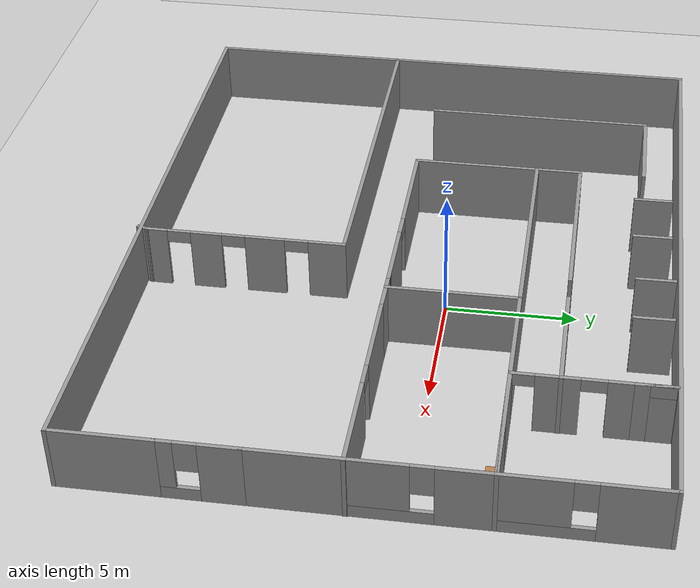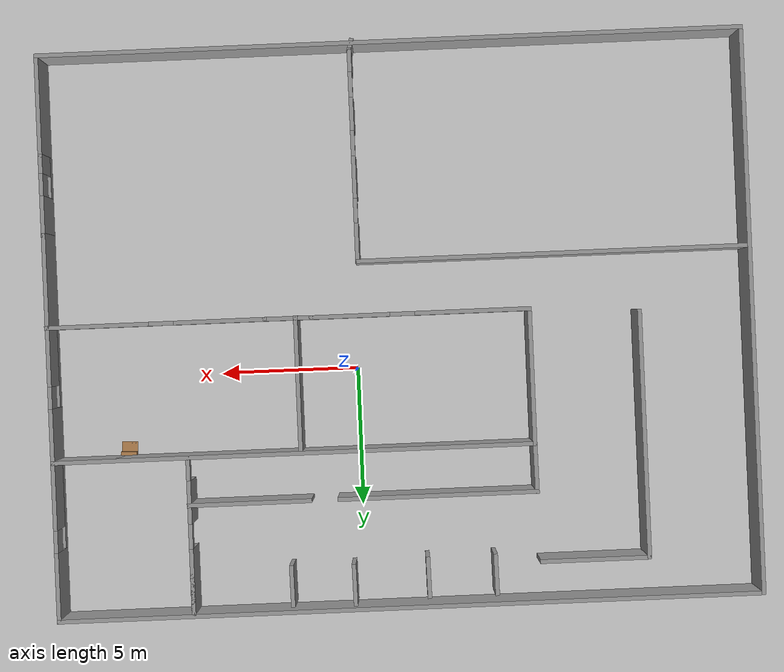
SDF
<sdf version="1.6">
 <world name="default">
  <light name="sun" type="directional">
   <pose>0 0 10 0 -0 0</pose>
   <diffuse>0.8 0.8 0.8 1</diffuse>
   <specular>0.2 0.2 0.2 1</specular>
   <attenuation>
    <range>1000</range>
    <constant>0.9</constant>
    <linear>0.01</linear>
    <quadratic>0.001</quadratic>
   </attenuation>
   <direction>-0.5 0.1 -0.9</direction>
  </light>
  <model name="ground_plane">
   <static>1</static>
   <link name="link">
    <collision name="collision">
     <geometry><plane><normal>0 0 1</normal><size>100 100</size></plane></geometry>
     <surface><friction><ode><mu>100</mu><mu2>50</mu2></ode></friction></surface>
    </collision>
    <visual name="visual">
     <cast_shadows>0</cast_shadows>
     <geometry><plane><normal>0 0 1</normal><size>100 100</size></plane></geometry>
     <material>
      <script><uri>file://media/materials/scripts/gazebo.material</uri><name>Gazebo/Grey</name></script>
     </material>
    </visual>
   </link>
  </model>
  <gravity>0 0 -9.8</gravity>
  <magnetic_field>6e-06 2.3e-05 -4.2e-05</magnetic_field>
  <atmosphere type="adiabatic"/>
  <physics name="default_physics" default="0" type="ode">
   <max_step_size>0.001</max_step_size>
   <real_time_factor>1</real_time_factor>
   <real_time_update_rate>1000</real_time_update_rate>
  </physics>
  <scene><ambient>0.4 0.4 0.4 1</ambient><background>0.7 0.7 0.7 1</background><shadows>1</shadows></scene>
  <spherical_coordinates>
   <surface_model>EARTH_WGS84</surface_model>
   <latitude_deg>0</latitude_deg>
   <longitude_deg>0</longitude_deg>
   <elevation>0</elevation>
   <heading_deg>0</heading_deg>
  </spherical_coordinates>
  <model name="factory_wall">
   <link name="Wall_11">
    <pose>8.76238 -0.332391 0 0 -0 0</pose>
    <visual name="Wall_11_Visual_0">
     <pose>-2.32414 0 1.25 0 -0 0</pose>
     <geometry><box><size>3.35171 0.15 2.5</size></box></geometry>
     <material>
      <script><uri>file://media/materials/scripts/gazebo.material</uri><name>Gazebo/Grey</name></script>
      <ambient>1 1 1 1</ambient>
      <shader type="pixel"/>
     </material>
     <meta><layer>0</layer></meta>
    </visual>
    <visual name="Wall_11_Visual_1">
     <pose>2.12586 0 1.25 0 -0 0</pose>
     <geometry><box><size>3.74829 0.15 2.5</size></box></geometry>
     <material>
      <script><uri>file://media/materials/scripts/gazebo.material</uri><name>Gazebo/Grey</name></script>
      <ambient>1 1 1 1</ambient>
      <shader type="pixel"/>
     </material>
     <meta><layer>0</layer></meta>
    </visual>
    <visual name="Wall_11_Visual_2">
     <pose>-0.198286 0 2.25 0 -0 0</pose>
     <geometry><box><size>0.9 0.15 0.5</size></box></geometry>
     <material>
      <script><uri>file://media/materials/scripts/gazebo.material</uri><name>Gazebo/Grey</name></script>
      <ambient>1 1 1 1</ambient>
      <shader type="pixel"/>
     </material>
     <meta><layer>0</layer></meta>
    </visual>
    <collision name="Wall_11_Collision_0">
     <pose>-2.32414 0 1.25 0 -0 0</pose>
     <geometry><box><size>3.35171 0.15 2.5</size></box></geometry>
     <surface>
      <friction>
       <ode><mu>1</mu><mu2>1</mu2><fdir1>0 0 0</fdir1><slip1>0</slip1><slip2>0</slip2></ode>
       <torsional>
        <coefficient>1</coefficient>
        <patch_radius>0</patch_radius>
        <surface_radius>0</surface_radius>
        <use_patch_radius>1</use_patch_radius>
        <ode><slip>0</slip></ode>
       </torsional>
      </friction>
      <bounce><restitution_coefficient>0</restitution_coefficient><threshold>1e+06</threshold></bounce>
      <contact>
       <collide_without_contact>0</collide_without_contact>
       <collide_without_contact_bitmask>1</collide_without_contact_bitmask>
       <collide_bitmask>1</collide_bitmask>
       <ode>
        <soft_cfm>0</soft_cfm>
        <soft_erp>0.2</soft_erp>
        <kp>1e+13</kp>
        <kd>1</kd>
        <max_vel>0.01</max_vel>
        <min_depth>0</min_depth>
       </ode>
       <bullet>
        <split_impulse>1</split_impulse>
        <split_impulse_penetration_threshold>-0.01</split_impulse_penetration_threshold>
        <soft_cfm>0</soft_cfm>
        <soft_erp>0.2</soft_erp>
        <kp>1e+13</kp>
        <kd>1</kd>
       </bullet>
      </contact>
     </surface>
    </collision>
    <collision name="Wall_11_Collision_1">
     <pose>2.12586 0 1.25 0 -0 0</pose>
     <geometry><box><size>3.74829 0.15 2.5</size></box></geometry>
     <surface>
      <friction>
       <ode><mu>1</mu><mu2>1</mu2><fdir1>0 0 0</fdir1><slip1>0</slip1><slip2>0</slip2></ode>
       <torsional>
        <coefficient>1</coefficient>
        <patch_radius>0</patch_radius>
        <surface_radius>0</surface_radius>
        <use_patch_radius>1</use_patch_radius>
        <ode><slip>0</slip></ode>
       </torsional>
      </friction>
      <bounce><restitution_coefficient>0</restitution_coefficient><threshold>1e+06</threshold></bounce>
      <contact>
       <collide_without_contact>0</collide_without_contact>
       <collide_without_contact_bitmask>1</collide_without_contact_bitmask>
       <collide_bitmask>1</collide_bitmask>
       <ode>
        <soft_cfm>0</soft_cfm>
        <soft_erp>0.2</soft_erp>
        <kp>1e+13</kp>
        <kd>1</kd>
        <max_vel>0.01</max_vel>
        <min_depth>0</min_depth>
       </ode>
       <bullet>
        <split_impulse>1</split_impulse>
        <split_impulse_penetration_threshold>-0.01</split_impulse_penetration_threshold>
        <soft_cfm>0</soft_cfm>
        <soft_erp>0.2</soft_erp>
        <kp>1e+13</kp>
        <kd>1</kd>
       </bullet>
      </contact>
     </surface>
    </collision>
    <collision name="Wall_11_Collision_2">
     <pose>-0.198286 0 2.25 0 -0 0</pose>
     <geometry><box><size>0.9 0.15 0.5</size></box></geometry>
     <surface>
      <friction>
       <ode><mu>1</mu><mu2>1</mu2><fdir1>0 0 0</fdir1><slip1>0</slip1><slip2>0</slip2></ode>
       <torsional>
        <coefficient>1</coefficient>
        <patch_radius>0</patch_radius>
        <surface_radius>0</surface_radius>
        <use_patch_radius>1</use_patch_radius>
        <ode><slip>0</slip></ode>
       </torsional>
      </friction>
      <bounce><restitution_coefficient>0</restitution_coefficient><threshold>1e+06</threshold></bounce>
      <contact>
       <collide_without_contact>0</collide_without_contact>
       <collide_without_contact_bitmask>1</collide_without_contact_bitmask>
       <collide_bitmask>1</collide_bitmask>
       <ode>
        <soft_cfm>0</soft_cfm>
        <soft_erp>0.2</soft_erp>
        <kp>1e+13</kp>
        <kd>1</kd>
        <max_vel>0.01</max_vel>
        <min_depth>0</min_depth>
       </ode>
       <bullet>
        <split_impulse>1</split_impulse>
        <split_impulse_penetration_threshold>-0.01</split_impulse_penetration_threshold>
        <soft_cfm>0</soft_cfm>
        <soft_erp>0.2</soft_erp>
        <kp>1e+13</kp>
        <kd>1</kd>
       </bullet>
      </contact>
     </surface>
    </collision>
   </link>
   <link name="Wall_13">
    <pose>-0.762375 -0.322535 0 0 -0 3.14159</pose>
    <visual name="Wall_13_Visual_0">
     <pose>-2.55074 0 1.25 0 -0 0</pose>
     <geometry><box><size>2.89852 0.15 2.5</size></box></geometry>
     <material>
      <script><uri>file://media/materials/scripts/gazebo.material</uri><name>Gazebo/Grey</name></script>
      <ambient>1 1 1 1</ambient>
      <shader type="pixel"/>
     </material>
     <meta><layer>0</layer></meta>
    </visual>
    <visual name="Wall_13_Visual_1">
     <pose>1.89926 0 1.25 0 -0 0</pose>
     <geometry><box><size>4.20148 0.15 2.5</size></box></geometry>
     <material>
      <script><uri>file://media/materials/scripts/gazebo.material</uri><name>Gazebo/Grey</name></script>
      <ambient>1 1 1 1</ambient>
      <shader type="pixel"/>
     </material>
     <meta><layer>0</layer></meta>
    </visual>
    <visual name="Wall_13_Visual_2">
     <pose>-0.651482 0 2.25 0 -0 0</pose>
     <geometry><box><size>0.9 0.15 0.5</size></box></geometry>
     <material>
      <script><uri>file://media/materials/scripts/gazebo.material</uri><name>Gazebo/Grey</name></script>
      <ambient>1 1 1 1</ambient>
      <shader type="pixel"/>
     </material>
     <meta><layer>0</layer></meta>
    </visual>
    <collision name="Wall_13_Collision_0">
     <pose>-2.55074 0 1.25 0 -0 0</pose>
     <geometry><box><size>2.89852 0.15 2.5</size></box></geometry>
     <surface>
      <friction>
       <ode><mu>1</mu><mu2>1</mu2><fdir1>0 0 0</fdir1><slip1>0</slip1><slip2>0</slip2></ode>
       <torsional>
        <coefficient>1</coefficient>
        <patch_radius>0</patch_radius>
        <surface_radius>0</surface_radius>
        <use_patch_radius>1</use_patch_radius>
        <ode><slip>0</slip></ode>
       </torsional>
      </friction>
      <bounce><restitution_coefficient>0</restitution_coefficient><threshold>1e+06</threshold></bounce>
      <contact>
       <collide_without_contact>0</collide_without_contact>
       <collide_without_contact_bitmask>1</collide_without_contact_bitmask>
       <collide_bitmask>1</collide_bitmask>
       <ode>
        <soft_cfm>0</soft_cfm>
        <soft_erp>0.2</soft_erp>
        <kp>1e+13</kp>
        <kd>1</kd>
        <max_vel>0.01</max_vel>
        <min_depth>0</min_depth>
       </ode>
       <bullet>
        <split_impulse>1</split_impulse>
        <split_impulse_penetration_threshold>-0.01</split_impulse_penetration_threshold>
        <soft_cfm>0</soft_cfm>
        <soft_erp>0.2</soft_erp>
        <kp>1e+13</kp>
        <kd>1</kd>
       </bullet>
      </contact>
     </surface>
    </collision>
    <collision name="Wall_13_Collision_1">
     <pose>1.89926 0 1.25 0 -0 0</pose>
     <geometry><box><size>4.20148 0.15 2.5</size></box></geometry>
     <surface>
      <friction>
       <ode><mu>1</mu><mu2>1</mu2><fdir1>0 0 0</fdir1><slip1>0</slip1><slip2>0</slip2></ode>
       <torsional>
        <coefficient>1</coefficient>
        <patch_radius>0</patch_radius>
        <surface_radius>0</surface_radius>
        <use_patch_radius>1</use_patch_radius>
        <ode><slip>0</slip></ode>
       </torsional>
      </friction>
      <bounce><restitution_coefficient>0</restitution_coefficient><threshold>1e+06</threshold></bounce>
      <contact>
       <collide_without_contact>0</collide_without_contact>
       <collide_without_contact_bitmask>1</collide_without_contact_bitmask>
       <collide_bitmask>1</collide_bitmask>
       <ode>
        <soft_cfm>0</soft_cfm>
        <soft_erp>0.2</soft_erp>
        <kp>1e+13</kp>
        <kd>1</kd>
        <max_vel>0.01</max_vel>
        <min_depth>0</min_depth>
       </ode>
       <bullet>
        <split_impulse>1</split_impulse>
        <split_impulse_penetration_threshold>-0.01</split_impulse_penetration_threshold>
        <soft_cfm>0</soft_cfm>
        <soft_erp>0.2</soft_erp>
        <kp>1e+13</kp>
        <kd>1</kd>
       </bullet>
      </contact>
     </surface>
    </collision>
    <collision name="Wall_13_Collision_2">
     <pose>-0.651482 0 2.25 0 -0 0</pose>
     <geometry><box><size>0.9 0.15 0.5</size></box></geometry>
     <surface>
      <friction>
       <ode><mu>1</mu><mu2>1</mu2><fdir1>0 0 0</fdir1><slip1>0</slip1><slip2>0</slip2></ode>
       <torsional>
        <coefficient>1</coefficient>
        <patch_radius>0</patch_radius>
        <surface_radius>0</surface_radius>
        <use_patch_radius>1</use_patch_radius>
        <ode><slip>0</slip></ode>
       </torsional>
      </friction>
      <bounce><restitution_coefficient>0</restitution_coefficient><threshold>1e+06</threshold></bounce>
      <contact>
       <collide_without_contact>0</collide_without_contact>
       <collide_without_contact_bitmask>1</collide_without_contact_bitmask>
       <collide_bitmask>1</collide_bitmask>
       <ode>
        <soft_cfm>0</soft_cfm>
        <soft_erp>0.2</soft_erp>
        <kp>1e+13</kp>
        <kd>1</kd>
        <max_vel>0.01</max_vel>
        <min_depth>0</min_depth>
       </ode>
       <bullet>
        <split_impulse>1</split_impulse>
        <split_impulse_penetration_threshold>-0.01</split_impulse_penetration_threshold>
        <soft_cfm>0</soft_cfm>
        <soft_erp>0.2</soft_erp>
        <kp>1e+13</kp>
        <kd>1</kd>
       </bullet>
      </contact>
     </surface>
    </collision>
   </link>
   <link name="Wall_15">
    <pose>-4.68738 2.10247 0 0 -0 1.5708</pose>
    <visual name="Wall_15_Visual">
     <pose>0 0 1.25 0 -0 0</pose>
     <geometry><box><size>5 0.15 2.5</size></box></geometry>
     <material>
      <script><uri>file://media/materials/scripts/gazebo.material</uri><name>Gazebo/Grey</name></script>
      <ambient>1 1 1 1</ambient>
      <shader type="pixel"/>
     </material>
     <meta><layer>0</layer></meta>
    </visual>
    <collision name="Wall_15_Collision">
     <pose>0 0 1.25 0 -0 0</pose>
     <geometry><box><size>5 0.15 2.5</size></box></geometry>
     <surface>
      <friction>
       <ode><mu>1</mu><mu2>1</mu2><fdir1>0 0 0</fdir1><slip1>0</slip1><slip2>0</slip2></ode>
       <torsional>
        <coefficient>1</coefficient>
        <patch_radius>0</patch_radius>
        <surface_radius>0</surface_radius>
        <use_patch_radius>1</use_patch_radius>
        <ode><slip>0</slip></ode>
       </torsional>
      </friction>
      <bounce><restitution_coefficient>0</restitution_coefficient><threshold>1e+06</threshold></bounce>
      <contact>
       <collide_without_contact>0</collide_without_contact>
       <collide_without_contact_bitmask>1</collide_without_contact_bitmask>
       <collide_bitmask>1</collide_bitmask>
       <ode>
        <soft_cfm>0</soft_cfm>
        <soft_erp>0.2</soft_erp>
        <kp>1e+13</kp>
        <kd>1</kd>
        <max_vel>0.01</max_vel>
        <min_depth>0</min_depth>
       </ode>
       <bullet>
        <split_impulse>1</split_impulse>
        <split_impulse_penetration_threshold>-0.01</split_impulse_penetration_threshold>
        <soft_cfm>0</soft_cfm>
        <soft_erp>0.2</soft_erp>
        <kp>1e+13</kp>
        <kd>1</kd>
       </bullet>
      </contact>
     </surface>
    </collision>
   </link>
   <link name="Wall_16">
    <pose>3.98762 4.52747 0 0 -0 0</pose>
    <visual name="Wall_16_Visual">
     <pose>0 0 1.25 0 -0 0</pose>
     <geometry><box><size>17.5 0.15 2.5</size></box></geometry>
     <material>
      <script><uri>file://media/materials/scripts/gazebo.material</uri><name>Gazebo/Grey</name></script>
      <ambient>1 1 1 1</ambient>
      <shader type="pixel"/>
     </material>
     <meta><layer>0</layer></meta>
    </visual>
    <collision name="Wall_16_Collision">
     <pose>0 0 1.25 0 -0 0</pose>
     <geometry><box><size>17.5 0.15 2.5</size></box></geometry>
     <surface>
      <friction>
       <ode><mu>1</mu><mu2>1</mu2><fdir1>0 0 0</fdir1><slip1>0</slip1><slip2>0</slip2></ode>
       <torsional>
        <coefficient>1</coefficient>
        <patch_radius>0</patch_radius>
        <surface_radius>0</surface_radius>
        <use_patch_radius>1</use_patch_radius>
        <ode><slip>0</slip></ode>
       </torsional>
      </friction>
      <bounce><restitution_coefficient>0</restitution_coefficient><threshold>1e+06</threshold></bounce>
      <contact>
       <collide_without_contact>0</collide_without_contact>
       <collide_without_contact_bitmask>1</collide_without_contact_bitmask>
       <collide_bitmask>1</collide_bitmask>
       <ode>
        <soft_cfm>0</soft_cfm>
        <soft_erp>0.2</soft_erp>
        <kp>1e+13</kp>
        <kd>1</kd>
        <max_vel>0.01</max_vel>
        <min_depth>0</min_depth>
       </ode>
       <bullet>
        <split_impulse>1</split_impulse>
        <split_impulse_penetration_threshold>-0.01</split_impulse_penetration_threshold>
        <soft_cfm>0</soft_cfm>
        <soft_erp>0.2</soft_erp>
        <kp>1e+13</kp>
        <kd>1</kd>
       </bullet>
      </contact>
     </surface>
    </collision>
   </link>
   <link name="Wall_17">
    <pose>12.6626 2.10247 0 0 0 -1.5708</pose>
    <visual name="Wall_17_Visual_0">
     <pose>-1.48655 0 1.25 0 -0 0</pose>
     <geometry><box><size>2.0269 0.15 2.5</size></box></geometry>
     <material>
      <script><uri>file://media/materials/scripts/gazebo.material</uri><name>Gazebo/Grey</name></script>
      <ambient>1 1 1 1</ambient>
      <shader type="pixel"/>
     </material>
     <meta><layer>0</layer></meta>
    </visual>
    <visual name="Wall_17_Visual_1">
     <pose>1.01345 0 0.25 0 -0 0</pose>
     <geometry><box><size>2.9731 0.15 0.5</size></box></geometry>
     <material>
      <script><uri>file://media/materials/scripts/gazebo.material</uri><name>Gazebo/Grey</name></script>
      <ambient>1 1 1 1</ambient>
      <shader type="pixel"/>
     </material>
     <meta><layer>0</layer></meta>
    </visual>
    <visual name="Wall_17_Visual_2">
     <pose>1.41345 0 1.5 0 -0 0</pose>
     <geometry><box><size>2.1731 0.15 2</size></box></geometry>
     <material>
      <script><uri>file://media/materials/scripts/gazebo.material</uri><name>Gazebo/Grey</name></script>
      <ambient>1 1 1 1</ambient>
      <shader type="pixel"/>
     </material>
     <meta><layer>0</layer></meta>
    </visual>
    <visual name="Wall_17_Visual_3">
     <pose>-0.073103 0 1.9 0 -0 0</pose>
     <geometry><box><size>0.8 0.15 1.2</size></box></geometry>
     <material>
      <script><uri>file://media/materials/scripts/gazebo.material</uri><name>Gazebo/Grey</name></script>
      <ambient>1 1 1 1</ambient>
      <shader type="pixel"/>
     </material>
     <meta><layer>0</layer></meta>
    </visual>
    <collision name="Wall_17_Collision_0">
     <pose>-1.48655 0 1.25 0 -0 0</pose>
     <geometry><box><size>2.0269 0.15 2.5</size></box></geometry>
     <surface>
      <friction>
       <ode><mu>1</mu><mu2>1</mu2><fdir1>0 0 0</fdir1><slip1>0</slip1><slip2>0</slip2></ode>
       <torsional>
        <coefficient>1</coefficient>
        <patch_radius>0</patch_radius>
        <surface_radius>0</surface_radius>
        <use_patch_radius>1</use_patch_radius>
        <ode><slip>0</slip></ode>
       </torsional>
      </friction>
      <bounce><restitution_coefficient>0</restitution_coefficient><threshold>1e+06</threshold></bounce>
      <contact>
       <collide_without_contact>0</collide_without_contact>
       <collide_without_contact_bitmask>1</collide_without_contact_bitmask>
       <collide_bitmask>1</collide_bitmask>
       <ode>
        <soft_cfm>0</soft_cfm>
        <soft_erp>0.2</soft_erp>
        <kp>1e+13</kp>
        <kd>1</kd>
        <max_vel>0.01</max_vel>
        <min_depth>0</min_depth>
       </ode>
       <bullet>
        <split_impulse>1</split_impulse>
        <split_impulse_penetration_threshold>-0.01</split_impulse_penetration_threshold>
        <soft_cfm>0</soft_cfm>
        <soft_erp>0.2</soft_erp>
        <kp>1e+13</kp>
        <kd>1</kd>
       </bullet>
      </contact>
     </surface>
    </collision>
    <collision name="Wall_17_Collision_1">
     <pose>1.01345 0 0.25 0 -0 0</pose>
     <geometry><box><size>2.9731 0.15 0.5</size></box></geometry>
     <surface>
      <friction>
       <ode><mu>1</mu><mu2>1</mu2><fdir1>0 0 0</fdir1><slip1>0</slip1><slip2>0</slip2></ode>
       <torsional>
        <coefficient>1</coefficient>
        <patch_radius>0</patch_radius>
        <surface_radius>0</surface_radius>
        <use_patch_radius>1</use_patch_radius>
        <ode><slip>0</slip></ode>
       </torsional>
      </friction>
      <bounce><restitution_coefficient>0</restitution_coefficient><threshold>1e+06</threshold></bounce>
      <contact>
       <collide_without_contact>0</collide_without_contact>
       <collide_without_contact_bitmask>1</collide_without_contact_bitmask>
       <collide_bitmask>1</collide_bitmask>
       <ode>
        <soft_cfm>0</soft_cfm>
        <soft_erp>0.2</soft_erp>
        <kp>1e+13</kp>
        <kd>1</kd>
        <max_vel>0.01</max_vel>
        <min_depth>0</min_depth>
       </ode>
       <bullet>
        <split_impulse>1</split_impulse>
        <split_impulse_penetration_threshold>-0.01</split_impulse_penetration_threshold>
        <soft_cfm>0</soft_cfm>
        <soft_erp>0.2</soft_erp>
        <kp>1e+13</kp>
        <kd>1</kd>
       </bullet>
      </contact>
     </surface>
    </collision>
    <collision name="Wall_17_Collision_2">
     <pose>1.41345 0 1.5 0 -0 0</pose>
     <geometry><box><size>2.1731 0.15 2</size></box></geometry>
     <surface>
      <friction>
       <ode><mu>1</mu><mu2>1</mu2><fdir1>0 0 0</fdir1><slip1>0</slip1><slip2>0</slip2></ode>
       <torsional>
        <coefficient>1</coefficient>
        <patch_radius>0</patch_radius>
        <surface_radius>0</surface_radius>
        <use_patch_radius>1</use_patch_radius>
        <ode><slip>0</slip></ode>
       </torsional>
      </friction>
      <bounce><restitution_coefficient>0</restitution_coefficient><threshold>1e+06</threshold></bounce>
      <contact>
       <collide_without_contact>0</collide_without_contact>
       <collide_without_contact_bitmask>1</collide_without_contact_bitmask>
       <collide_bitmask>1</collide_bitmask>
       <ode>
        <soft_cfm>0</soft_cfm>
        <soft_erp>0.2</soft_erp>
        <kp>1e+13</kp>
        <kd>1</kd>
        <max_vel>0.01</max_vel>
        <min_depth>0</min_depth>
       </ode>
       <bullet>
        <split_impulse>1</split_impulse>
        <split_impulse_penetration_threshold>-0.01</split_impulse_penetration_threshold>
        <soft_cfm>0</soft_cfm>
        <soft_erp>0.2</soft_erp>
        <kp>1e+13</kp>
        <kd>1</kd>
       </bullet>
      </contact>
     </surface>
    </collision>
    <collision name="Wall_17_Collision_3">
     <pose>-0.073103 0 1.9 0 -0 0</pose>
     <geometry><box><size>0.8 0.15 1.2</size></box></geometry>
     <surface>
      <friction>
       <ode><mu>1</mu><mu2>1</mu2><fdir1>0 0 0</fdir1><slip1>0</slip1><slip2>0</slip2></ode>
       <torsional>
        <coefficient>1</coefficient>
        <patch_radius>0</patch_radius>
        <surface_radius>0</surface_radius>
        <use_patch_radius>1</use_patch_radius>
        <ode><slip>0</slip></ode>
       </torsional>
      </friction>
      <bounce><restitution_coefficient>0</restitution_coefficient><threshold>1e+06</threshold></bounce>
      <contact>
       <collide_without_contact>0</collide_without_contact>
       <collide_without_contact_bitmask>1</collide_without_contact_bitmask>
       <collide_bitmask>1</collide_bitmask>
       <ode>
        <soft_cfm>0</soft_cfm>
        <soft_erp>0.2</soft_erp>
        <kp>1e+13</kp>
        <kd>1</kd>
        <max_vel>0.01</max_vel>
        <min_depth>0</min_depth>
       </ode>
       <bullet>
        <split_impulse>1</split_impulse>
        <split_impulse_penetration_threshold>-0.01</split_impulse_penetration_threshold>
        <soft_cfm>0</soft_cfm>
        <soft_erp>0.2</soft_erp>
        <kp>1e+13</kp>
        <kd>1</kd>
       </bullet>
      </contact>
     </surface>
    </collision>
   </link>
   <link name="Wall_19">
    <pose>12.6626 -1.99754 0 0 0 -1.5708</pose>
    <visual name="Wall_19_Visual">
     <pose>0 0 1.25 0 -0 0</pose>
     <geometry><box><size>3.5 0.15 2.5</size></box></geometry>
     <material>
      <script><uri>file://media/materials/scripts/gazebo.material</uri><name>Gazebo/Grey</name></script>
      <ambient>1 1 1 1</ambient>
      <shader type="pixel"/>
     </material>
     <meta><layer>0</layer></meta>
    </visual>
    <collision name="Wall_19_Collision">
     <pose>0 0 1.25 0 -0 0</pose>
     <geometry><box><size>3.5 0.15 2.5</size></box></geometry>
     <surface>
      <friction>
       <ode><mu>1</mu><mu2>1</mu2><fdir1>0 0 0</fdir1><slip1>0</slip1><slip2>0</slip2></ode>
       <torsional>
        <coefficient>1</coefficient>
        <patch_radius>0</patch_radius>
        <surface_radius>0</surface_radius>
        <use_patch_radius>1</use_patch_radius>
        <ode><slip>0</slip></ode>
       </torsional>
      </friction>
      <bounce><restitution_coefficient>0</restitution_coefficient><threshold>1e+06</threshold></bounce>
      <contact>
       <collide_without_contact>0</collide_without_contact>
       <collide_without_contact_bitmask>1</collide_without_contact_bitmask>
       <collide_bitmask>1</collide_bitmask>
       <ode>
        <soft_cfm>0</soft_cfm>
        <soft_erp>0.2</soft_erp>
        <kp>1e+13</kp>
        <kd>1</kd>
        <max_vel>0.01</max_vel>
        <min_depth>0</min_depth>
       </ode>
       <bullet>
        <split_impulse>1</split_impulse>
        <split_impulse_penetration_threshold>-0.01</split_impulse_penetration_threshold>
        <soft_cfm>0</soft_cfm>
        <soft_erp>0.2</soft_erp>
        <kp>1e+13</kp>
        <kd>1</kd>
       </bullet>
      </contact>
     </surface>
    </collision>
   </link>
   <link name="Wall_21">
    <pose>12.6626 -5.09753 0 0 0 -1.5708</pose>
    <visual name="Wall_21_Visual_0">
     <pose>-0.751301 0 1.25 0 -0 0</pose>
     <geometry><box><size>1.4974 0.15 2.5</size></box></geometry>
     <material>
      <script><uri>file://media/materials/scripts/gazebo.material</uri><name>Gazebo/Grey</name></script>
      <ambient>1 1 1 1</ambient>
      <shader type="pixel"/>
     </material>
     <meta><layer>0</layer></meta>
    </visual>
    <visual name="Wall_21_Visual_1">
     <pose>0.748699 0 0.25 0 -0 0</pose>
     <geometry><box><size>1.5026 0.15 0.5</size></box></geometry>
     <material>
      <script><uri>file://media/materials/scripts/gazebo.material</uri><name>Gazebo/Grey</name></script>
      <ambient>1 1 1 1</ambient>
      <shader type="pixel"/>
     </material>
     <meta><layer>0</layer></meta>
    </visual>
    <visual name="Wall_21_Visual_2">
     <pose>1.1487 0 1.5 0 -0 0</pose>
     <geometry><box><size>0.702603 0.15 2</size></box></geometry>
     <material>
      <script><uri>file://media/materials/scripts/gazebo.material</uri><name>Gazebo/Grey</name></script>
      <ambient>1 1 1 1</ambient>
      <shader type="pixel"/>
     </material>
     <meta><layer>0</layer></meta>
    </visual>
    <visual name="Wall_21_Visual_3">
     <pose>0.397397 0 1.9 0 -0 0</pose>
     <geometry><box><size>0.8 0.15 1.2</size></box></geometry>
     <material>
      <script><uri>file://media/materials/scripts/gazebo.material</uri><name>Gazebo/Grey</name></script>
      <ambient>1 1 1 1</ambient>
      <shader type="pixel"/>
     </material>
     <meta><layer>0</layer></meta>
    </visual>
    <collision name="Wall_21_Collision_0">
     <pose>-0.751301 0 1.25 0 -0 0</pose>
     <geometry><box><size>1.4974 0.15 2.5</size></box></geometry>
     <surface>
      <friction>
       <ode><mu>1</mu><mu2>1</mu2><fdir1>0 0 0</fdir1><slip1>0</slip1><slip2>0</slip2></ode>
       <torsional>
        <coefficient>1</coefficient>
        <patch_radius>0</patch_radius>
        <surface_radius>0</surface_radius>
        <use_patch_radius>1</use_patch_radius>
        <ode><slip>0</slip></ode>
       </torsional>
      </friction>
      <bounce><restitution_coefficient>0</restitution_coefficient><threshold>1e+06</threshold></bounce>
      <contact>
       <collide_without_contact>0</collide_without_contact>
       <collide_without_contact_bitmask>1</collide_without_contact_bitmask>
       <collide_bitmask>1</collide_bitmask>
       <ode>
        <soft_cfm>0</soft_cfm>
        <soft_erp>0.2</soft_erp>
        <kp>1e+13</kp>
        <kd>1</kd>
        <max_vel>0.01</max_vel>
        <min_depth>0</min_depth>
       </ode>
       <bullet>
        <split_impulse>1</split_impulse>
        <split_impulse_penetration_threshold>-0.01</split_impulse_penetration_threshold>
        <soft_cfm>0</soft_cfm>
        <soft_erp>0.2</soft_erp>
        <kp>1e+13</kp>
        <kd>1</kd>
       </bullet>
      </contact>
     </surface>
    </collision>
    <collision name="Wall_21_Collision_1">
     <pose>0.748699 0 0.25 0 -0 0</pose>
     <geometry><box><size>1.5026 0.15 0.5</size></box></geometry>
     <surface>
      <friction>
       <ode><mu>1</mu><mu2>1</mu2><fdir1>0 0 0</fdir1><slip1>0</slip1><slip2>0</slip2></ode>
       <torsional>
        <coefficient>1</coefficient>
        <patch_radius>0</patch_radius>
        <surface_radius>0</surface_radius>
        <use_patch_radius>1</use_patch_radius>
        <ode><slip>0</slip></ode>
       </torsional>
      </friction>
      <bounce><restitution_coefficient>0</restitution_coefficient><threshold>1e+06</threshold></bounce>
      <contact>
       <collide_without_contact>0</collide_without_contact>
       <collide_without_contact_bitmask>1</collide_without_contact_bitmask>
       <collide_bitmask>1</collide_bitmask>
       <ode>
        <soft_cfm>0</soft_cfm>
        <soft_erp>0.2</soft_erp>
        <kp>1e+13</kp>
        <kd>1</kd>
        <max_vel>0.01</max_vel>
        <min_depth>0</min_depth>
       </ode>
       <bullet>
        <split_impulse>1</split_impulse>
        <split_impulse_penetration_threshold>-0.01</split_impulse_penetration_threshold>
        <soft_cfm>0</soft_cfm>
        <soft_erp>0.2</soft_erp>
        <kp>1e+13</kp>
        <kd>1</kd>
       </bullet>
      </contact>
     </surface>
    </collision>
    <collision name="Wall_21_Collision_2">
     <pose>1.1487 0 1.5 0 -0 0</pose>
     <geometry><box><size>0.702603 0.15 2</size></box></geometry>
     <surface>
      <friction>
       <ode><mu>1</mu><mu2>1</mu2><fdir1>0 0 0</fdir1><slip1>0</slip1><slip2>0</slip2></ode>
       <torsional>
        <coefficient>1</coefficient>
        <patch_radius>0</patch_radius>
        <surface_radius>0</surface_radius>
        <use_patch_radius>1</use_patch_radius>
        <ode><slip>0</slip></ode>
       </torsional>
      </friction>
      <bounce><restitution_coefficient>0</restitution_coefficient><threshold>1e+06</threshold></bounce>
      <contact>
       <collide_without_contact>0</collide_without_contact>
       <collide_without_contact_bitmask>1</collide_without_contact_bitmask>
       <collide_bitmask>1</collide_bitmask>
       <ode>
        <soft_cfm>0</soft_cfm>
        <soft_erp>0.2</soft_erp>
        <kp>1e+13</kp>
        <kd>1</kd>
        <max_vel>0.01</max_vel>
        <min_depth>0</min_depth>
       </ode>
       <bullet>
        <split_impulse>1</split_impulse>
        <split_impulse_penetration_threshold>-0.01</split_impulse_penetration_threshold>
        <soft_cfm>0</soft_cfm>
        <soft_erp>0.2</soft_erp>
        <kp>1e+13</kp>
        <kd>1</kd>
       </bullet>
      </contact>
     </surface>
    </collision>
    <collision name="Wall_21_Collision_3">
     <pose>0.397397 0 1.9 0 -0 0</pose>
     <geometry><box><size>0.8 0.15 1.2</size></box></geometry>
     <surface>
      <friction>
       <ode><mu>1</mu><mu2>1</mu2><fdir1>0 0 0</fdir1><slip1>0</slip1><slip2>0</slip2></ode>
       <torsional>
        <coefficient>1</coefficient>
        <patch_radius>0</patch_radius>
        <surface_radius>0</surface_radius>
        <use_patch_radius>1</use_patch_radius>
        <ode><slip>0</slip></ode>
       </torsional>
      </friction>
      <bounce><restitution_coefficient>0</restitution_coefficient><threshold>1e+06</threshold></bounce>
      <contact>
       <collide_without_contact>0</collide_without_contact>
       <collide_without_contact_bitmask>1</collide_without_contact_bitmask>
       <collide_bitmask>1</collide_bitmask>
       <ode>
        <soft_cfm>0</soft_cfm>
        <soft_erp>0.2</soft_erp>
        <kp>1e+13</kp>
        <kd>1</kd>
        <max_vel>0.01</max_vel>
        <min_depth>0</min_depth>
       </ode>
       <bullet>
        <split_impulse>1</split_impulse>
        <split_impulse_penetration_threshold>-0.01</split_impulse_penetration_threshold>
        <soft_cfm>0</soft_cfm>
        <soft_erp>0.2</soft_erp>
        <kp>1e+13</kp>
        <kd>1</kd>
       </bullet>
      </contact>
     </surface>
    </collision>
   </link>
   <link name="Wall_23">
    <pose>12.6626 -8.32254 0 0 0 -1.5708</pose>
    <visual name="Wall_23_Visual">
     <pose>0 0 1.25 0 -0 0</pose>
     <geometry><box><size>3.75 0.15 2.5</size></box></geometry>
     <material>
      <script><uri>file://media/materials/scripts/gazebo.material</uri><name>Gazebo/Grey</name></script>
      <ambient>1 1 1 1</ambient>
      <shader type="pixel"/>
     </material>
     <meta><layer>0</layer></meta>
    </visual>
    <collision name="Wall_23_Collision">
     <pose>0 0 1.25 0 -0 0</pose>
     <geometry><box><size>3.75 0.15 2.5</size></box></geometry>
     <surface>
      <friction>
       <ode><mu>1</mu><mu2>1</mu2><fdir1>0 0 0</fdir1><slip1>0</slip1><slip2>0</slip2></ode>
       <torsional>
        <coefficient>1</coefficient>
        <patch_radius>0</patch_radius>
        <surface_radius>0</surface_radius>
        <use_patch_radius>1</use_patch_radius>
        <ode><slip>0</slip></ode>
       </torsional>
      </friction>
      <bounce><restitution_coefficient>0</restitution_coefficient><threshold>1e+06</threshold></bounce>
      <contact>
       <collide_without_contact>0</collide_without_contact>
       <collide_without_contact_bitmask>1</collide_without_contact_bitmask>
       <collide_bitmask>1</collide_bitmask>
       <ode>
        <soft_cfm>0</soft_cfm>
        <soft_erp>0.2</soft_erp>
        <kp>1e+13</kp>
        <kd>1</kd>
        <max_vel>0.01</max_vel>
        <min_depth>0</min_depth>
       </ode>
       <bullet>
        <split_impulse>1</split_impulse>
        <split_impulse_penetration_threshold>-0.01</split_impulse_penetration_threshold>
        <soft_cfm>0</soft_cfm>
        <soft_erp>0.2</soft_erp>
        <kp>1e+13</kp>
        <kd>1</kd>
       </bullet>
      </contact>
     </surface>
    </collision>
   </link>
   <link name="Wall_26">
    <pose>-0.012375 -10.1225 0 0 -0 3.14159</pose>
    <visual name="Wall_26_Visual">
     <pose>0 0 1.25 0 -0 0</pose>
     <geometry><box><size>25.5 0.15 2.5</size></box></geometry>
     <material>
      <script><uri>file://media/materials/scripts/gazebo.material</uri><name>Gazebo/Grey</name></script>
      <ambient>1 1 1 1</ambient>
      <shader type="pixel"/>
     </material>
     <meta><layer>0</layer></meta>
    </visual>
    <collision name="Wall_26_Collision">
     <pose>0 0 1.25 0 -0 0</pose>
     <geometry><box><size>25.5 0.15 2.5</size></box></geometry>
     <surface>
      <friction>
       <ode><mu>1</mu><mu2>1</mu2><fdir1>0 0 0</fdir1><slip1>0</slip1><slip2>0</slip2></ode>
       <torsional>
        <coefficient>1</coefficient>
        <patch_radius>0</patch_radius>
        <surface_radius>0</surface_radius>
        <use_patch_radius>1</use_patch_radius>
        <ode><slip>0</slip></ode>
       </torsional>
      </friction>
      <bounce><restitution_coefficient>0</restitution_coefficient><threshold>1e+06</threshold></bounce>
      <contact>
       <collide_without_contact>0</collide_without_contact>
       <collide_without_contact_bitmask>1</collide_without_contact_bitmask>
       <collide_bitmask>1</collide_bitmask>
       <ode>
        <soft_cfm>0</soft_cfm>
        <soft_erp>0.2</soft_erp>
        <kp>1e+13</kp>
        <kd>1</kd>
        <max_vel>0.01</max_vel>
        <min_depth>0</min_depth>
       </ode>
       <bullet>
        <split_impulse>1</split_impulse>
        <split_impulse_penetration_threshold>-0.01</split_impulse_penetration_threshold>
        <soft_cfm>0</soft_cfm>
        <soft_erp>0.2</soft_erp>
        <kp>1e+13</kp>
        <kd>1</kd>
       </bullet>
      </contact>
     </surface>
    </collision>
   </link>
   <link name="Wall_27">
    <pose>-12.6874 0.052465 0 0 -0 1.5708</pose>
    <visual name="Wall_27_Visual">
     <pose>0 0 1.25 0 -0 0</pose>
     <geometry><box><size>20.5 0.15 2.5</size></box></geometry>
     <material>
      <script><uri>file://media/materials/scripts/gazebo.material</uri><name>Gazebo/Grey</name></script>
      <ambient>1 1 1 1</ambient>
      <shader type="pixel"/>
     </material>
     <meta><layer>0</layer></meta>
    </visual>
    <collision name="Wall_27_Collision">
     <pose>0 0 1.25 0 -0 0</pose>
     <geometry><box><size>20.5 0.15 2.5</size></box></geometry>
     <surface>
      <friction>
       <ode><mu>1</mu><mu2>1</mu2><fdir1>0 0 0</fdir1><slip1>0</slip1><slip2>0</slip2></ode>
       <torsional>
        <coefficient>1</coefficient>
        <patch_radius>0</patch_radius>
        <surface_radius>0</surface_radius>
        <use_patch_radius>1</use_patch_radius>
        <ode><slip>0</slip></ode>
       </torsional>
      </friction>
      <bounce><restitution_coefficient>0</restitution_coefficient><threshold>1e+06</threshold></bounce>
      <contact>
       <collide_without_contact>0</collide_without_contact>
       <collide_without_contact_bitmask>1</collide_without_contact_bitmask>
       <collide_bitmask>1</collide_bitmask>
       <ode>
        <soft_cfm>0</soft_cfm>
        <soft_erp>0.2</soft_erp>
        <kp>1e+13</kp>
        <kd>1</kd>
        <max_vel>0.01</max_vel>
        <min_depth>0</min_depth>
       </ode>
       <bullet>
        <split_impulse>1</split_impulse>
        <split_impulse_penetration_threshold>-0.01</split_impulse_penetration_threshold>
        <soft_cfm>0</soft_cfm>
        <soft_erp>0.2</soft_erp>
        <kp>1e+13</kp>
        <kd>1</kd>
       </bullet>
      </contact>
     </surface>
    </collision>
   </link>
   <link name="Wall_29">
    <pose>-0.012375 10.2275 0 0 -0 0</pose>
    <visual name="Wall_29_Visual">
     <pose>0 0 1.25 0 -0 0</pose>
     <geometry><box><size>25.5 0.15 2.5</size></box></geometry>
     <material>
      <script><uri>file://media/materials/scripts/gazebo.material</uri><name>Gazebo/Grey</name></script>
      <ambient>1 1 1 1</ambient>
      <shader type="pixel"/>
     </material>
     <meta><layer>0</layer></meta>
    </visual>
    <collision name="Wall_29_Collision">
     <pose>0 0 1.25 0 -0 0</pose>
     <geometry><box><size>25.5 0.15 2.5</size></box></geometry>
     <surface>
      <friction>
       <ode><mu>1</mu><mu2>1</mu2><fdir1>0 0 0</fdir1><slip1>0</slip1><slip2>0</slip2></ode>
       <torsional>
        <coefficient>1</coefficient>
        <patch_radius>0</patch_radius>
        <surface_radius>0</surface_radius>
        <use_patch_radius>1</use_patch_radius>
        <ode><slip>0</slip></ode>
       </torsional>
      </friction>
      <bounce><restitution_coefficient>0</restitution_coefficient><threshold>1e+06</threshold></bounce>
      <contact>
       <collide_without_contact>0</collide_without_contact>
       <collide_without_contact_bitmask>1</collide_without_contact_bitmask>
       <collide_bitmask>1</collide_bitmask>
       <ode>
        <soft_cfm>0</soft_cfm>
        <soft_erp>0.2</soft_erp>
        <kp>1e+13</kp>
        <kd>1</kd>
        <max_vel>0.01</max_vel>
        <min_depth>0</min_depth>
       </ode>
       <bullet>
        <split_impulse>1</split_impulse>
        <split_impulse_penetration_threshold>-0.01</split_impulse_penetration_threshold>
        <soft_cfm>0</soft_cfm>
        <soft_erp>0.2</soft_erp>
        <kp>1e+13</kp>
        <kd>1</kd>
       </bullet>
      </contact>
     </surface>
    </collision>
   </link>
   <link name="Wall_30">
    <pose>12.6626 7.37746 0 0 0 -1.5708</pose>
    <visual name="Wall_30_Visual_0">
     <pose>-1.65365 0 1.25 0 -0 0</pose>
     <geometry><box><size>2.5427 0.15 2.5</size></box></geometry>
     <material>
      <script><uri>file://media/materials/scripts/gazebo.material</uri><name>Gazebo/Grey</name></script>
      <ambient>1 1 1 1</ambient>
      <shader type="pixel"/>
     </material>
     <meta><layer>0</layer></meta>
    </visual>
    <visual name="Wall_30_Visual_1">
     <pose>1.27135 0 0.25 0 -0 0</pose>
     <geometry><box><size>3.3073 0.15 0.5</size></box></geometry>
     <material>
      <script><uri>file://media/materials/scripts/gazebo.material</uri><name>Gazebo/Grey</name></script>
      <ambient>1 1 1 1</ambient>
      <shader type="pixel"/>
     </material>
     <meta><layer>0</layer></meta>
    </visual>
    <visual name="Wall_30_Visual_2">
     <pose>1.67135 0 1.5 0 -0 0</pose>
     <geometry><box><size>2.5073 0.15 2</size></box></geometry>
     <material>
      <script><uri>file://media/materials/scripts/gazebo.material</uri><name>Gazebo/Grey</name></script>
      <ambient>1 1 1 1</ambient>
      <shader type="pixel"/>
     </material>
     <meta><layer>0</layer></meta>
    </visual>
    <visual name="Wall_30_Visual_3">
     <pose>0.017697 0 1.9 0 -0 0</pose>
     <geometry><box><size>0.8 0.15 1.2</size></box></geometry>
     <material>
      <script><uri>file://media/materials/scripts/gazebo.material</uri><name>Gazebo/Grey</name></script>
      <ambient>1 1 1 1</ambient>
      <shader type="pixel"/>
     </material>
     <meta><layer>0</layer></meta>
    </visual>
    <collision name="Wall_30_Collision_0">
     <pose>-1.65365 0 1.25 0 -0 0</pose>
     <geometry><box><size>2.5427 0.15 2.5</size></box></geometry>
     <surface>
      <friction>
       <ode><mu>1</mu><mu2>1</mu2><fdir1>0 0 0</fdir1><slip1>0</slip1><slip2>0</slip2></ode>
       <torsional>
        <coefficient>1</coefficient>
        <patch_radius>0</patch_radius>
        <surface_radius>0</surface_radius>
        <use_patch_radius>1</use_patch_radius>
        <ode><slip>0</slip></ode>
       </torsional>
      </friction>
      <bounce><restitution_coefficient>0</restitution_coefficient><threshold>1e+06</threshold></bounce>
      <contact>
       <collide_without_contact>0</collide_without_contact>
       <collide_without_contact_bitmask>1</collide_without_contact_bitmask>
       <collide_bitmask>1</collide_bitmask>
       <ode>
        <soft_cfm>0</soft_cfm>
        <soft_erp>0.2</soft_erp>
        <kp>1e+13</kp>
        <kd>1</kd>
        <max_vel>0.01</max_vel>
        <min_depth>0</min_depth>
       </ode>
       <bullet>
        <split_impulse>1</split_impulse>
        <split_impulse_penetration_threshold>-0.01</split_impulse_penetration_threshold>
        <soft_cfm>0</soft_cfm>
        <soft_erp>0.2</soft_erp>
        <kp>1e+13</kp>
        <kd>1</kd>
       </bullet>
      </contact>
     </surface>
    </collision>
    <collision name="Wall_30_Collision_1">
     <pose>1.27135 0 0.25 0 -0 0</pose>
     <geometry><box><size>3.3073 0.15 0.5</size></box></geometry>
     <surface>
      <friction>
       <ode><mu>1</mu><mu2>1</mu2><fdir1>0 0 0</fdir1><slip1>0</slip1><slip2>0</slip2></ode>
       <torsional>
        <coefficient>1</coefficient>
        <patch_radius>0</patch_radius>
        <surface_radius>0</surface_radius>
        <use_patch_radius>1</use_patch_radius>
        <ode><slip>0</slip></ode>
       </torsional>
      </friction>
      <bounce><restitution_coefficient>0</restitution_coefficient><threshold>1e+06</threshold></bounce>
      <contact>
       <collide_without_contact>0</collide_without_contact>
       <collide_without_contact_bitmask>1</collide_without_contact_bitmask>
       <collide_bitmask>1</collide_bitmask>
       <ode>
        <soft_cfm>0</soft_cfm>
        <soft_erp>0.2</soft_erp>
        <kp>1e+13</kp>
        <kd>1</kd>
        <max_vel>0.01</max_vel>
        <min_depth>0</min_depth>
       </ode>
       <bullet>
        <split_impulse>1</split_impulse>
        <split_impulse_penetration_threshold>-0.01</split_impulse_penetration_threshold>
        <soft_cfm>0</soft_cfm>
        <soft_erp>0.2</soft_erp>
        <kp>1e+13</kp>
        <kd>1</kd>
       </bullet>
      </contact>
     </surface>
    </collision>
    <collision name="Wall_30_Collision_2">
     <pose>1.67135 0 1.5 0 -0 0</pose>
     <geometry><box><size>2.5073 0.15 2</size></box></geometry>
     <surface>
      <friction>
       <ode><mu>1</mu><mu2>1</mu2><fdir1>0 0 0</fdir1><slip1>0</slip1><slip2>0</slip2></ode>
       <torsional>
        <coefficient>1</coefficient>
        <patch_radius>0</patch_radius>
        <surface_radius>0</surface_radius>
        <use_patch_radius>1</use_patch_radius>
        <ode><slip>0</slip></ode>
       </torsional>
      </friction>
      <bounce><restitution_coefficient>0</restitution_coefficient><threshold>1e+06</threshold></bounce>
      <contact>
       <collide_without_contact>0</collide_without_contact>
       <collide_without_contact_bitmask>1</collide_without_contact_bitmask>
       <collide_bitmask>1</collide_bitmask>
       <ode>
        <soft_cfm>0</soft_cfm>
        <soft_erp>0.2</soft_erp>
        <kp>1e+13</kp>
        <kd>1</kd>
        <max_vel>0.01</max_vel>
        <min_depth>0</min_depth>
       </ode>
       <bullet>
        <split_impulse>1</split_impulse>
        <split_impulse_penetration_threshold>-0.01</split_impulse_penetration_threshold>
        <soft_cfm>0</soft_cfm>
        <soft_erp>0.2</soft_erp>
        <kp>1e+13</kp>
        <kd>1</kd>
       </bullet>
      </contact>
     </surface>
    </collision>
    <collision name="Wall_30_Collision_3">
     <pose>0.017697 0 1.9 0 -0 0</pose>
     <geometry><box><size>0.8 0.15 1.2</size></box></geometry>
     <surface>
      <friction>
       <ode><mu>1</mu><mu2>1</mu2><fdir1>0 0 0</fdir1><slip1>0</slip1><slip2>0</slip2></ode>
       <torsional>
        <coefficient>1</coefficient>
        <patch_radius>0</patch_radius>
        <surface_radius>0</surface_radius>
        <use_patch_radius>1</use_patch_radius>
        <ode><slip>0</slip></ode>
       </torsional>
      </friction>
      <bounce><restitution_coefficient>0</restitution_coefficient><threshold>1e+06</threshold></bounce>
      <contact>
       <collide_without_contact>0</collide_without_contact>
       <collide_without_contact_bitmask>1</collide_without_contact_bitmask>
       <collide_bitmask>1</collide_bitmask>
       <ode>
        <soft_cfm>0</soft_cfm>
        <soft_erp>0.2</soft_erp>
        <kp>1e+13</kp>
        <kd>1</kd>
        <max_vel>0.01</max_vel>
        <min_depth>0</min_depth>
       </ode>
       <bullet>
        <split_impulse>1</split_impulse>
        <split_impulse_penetration_threshold>-0.01</split_impulse_penetration_threshold>
        <soft_cfm>0</soft_cfm>
        <soft_erp>0.2</soft_erp>
        <kp>1e+13</kp>
        <kd>1</kd>
       </bullet>
      </contact>
     </surface>
    </collision>
   </link>
   <link name="Wall_32">
    <pose>10.2376 4.52747 0 0 -0 3.14159</pose>
    <visual name="Wall_32_Visual">
     <pose>0 0 1.25 0 -0 0</pose>
     <geometry><box><size>5 0.15 2.5</size></box></geometry>
     <material>
      <script><uri>file://media/materials/scripts/gazebo.material</uri><name>Gazebo/Grey</name></script>
      <ambient>1 1 1 1</ambient>
      <shader type="pixel"/>
     </material>
     <meta><layer>0</layer></meta>
    </visual>
    <collision name="Wall_32_Collision">
     <pose>0 0 1.25 0 -0 0</pose>
     <geometry><box><size>5 0.15 2.5</size></box></geometry>
     <surface>
      <friction>
       <ode><mu>1</mu><mu2>1</mu2><fdir1>0 0 0</fdir1><slip1>0</slip1><slip2>0</slip2></ode>
       <torsional>
        <coefficient>1</coefficient>
        <patch_radius>0</patch_radius>
        <surface_radius>0</surface_radius>
        <use_patch_radius>1</use_patch_radius>
        <ode><slip>0</slip></ode>
       </torsional>
      </friction>
      <bounce><restitution_coefficient>0</restitution_coefficient><threshold>1e+06</threshold></bounce>
      <contact>
       <collide_without_contact>0</collide_without_contact>
       <collide_without_contact_bitmask>1</collide_without_contact_bitmask>
       <collide_bitmask>1</collide_bitmask>
       <ode>
        <soft_cfm>0</soft_cfm>
        <soft_erp>0.2</soft_erp>
        <kp>1e+13</kp>
        <kd>1</kd>
        <max_vel>0.01</max_vel>
        <min_depth>0</min_depth>
       </ode>
       <bullet>
        <split_impulse>1</split_impulse>
        <split_impulse_penetration_threshold>-0.01</split_impulse_penetration_threshold>
        <soft_cfm>0</soft_cfm>
        <soft_erp>0.2</soft_erp>
        <kp>1e+13</kp>
        <kd>1</kd>
       </bullet>
      </contact>
     </surface>
    </collision>
   </link>
   <link name="Wall_33">
    <pose>7.81262 7.32747 0 0 -0 1.5708</pose>
    <visual name="Wall_33_Visual_0">
     <pose>-2.86985 0 1.25 0 -0 0</pose>
     <geometry><box><size>0.010298 0.15 2.5</size></box></geometry>
     <material>
      <script><uri>file://media/materials/scripts/gazebo.material</uri><name>Gazebo/Grey</name></script>
      <ambient>1 1 1 1</ambient>
      <shader type="pixel"/>
     </material>
     <meta><layer>0</layer></meta>
    </visual>
    <visual name="Wall_33_Visual_1">
     <pose>-1.19 0 1.25 0 -0 0</pose>
     <geometry><box><size>1.54941 0.15 2.5</size></box></geometry>
     <material>
      <script><uri>file://media/materials/scripts/gazebo.material</uri><name>Gazebo/Grey</name></script>
      <ambient>1 1 1 1</ambient>
      <shader type="pixel"/>
     </material>
     <meta><layer>0</layer></meta>
    </visual>
    <visual name="Wall_33_Visual_2">
     <pose>1.67985 0 1.25 0 -0 0</pose>
     <geometry><box><size>2.3903 0.15 2.5</size></box></geometry>
     <material>
      <script><uri>file://media/materials/scripts/gazebo.material</uri><name>Gazebo/Grey</name></script>
      <ambient>1 1 1 1</ambient>
      <shader type="pixel"/>
     </material>
     <meta><layer>0</layer></meta>
    </visual>
    <visual name="Wall_33_Visual_3">
     <pose>-2.4147 0 2.25 0 -0 0</pose>
     <geometry><box><size>0.9 0.15 0.5</size></box></geometry>
     <material>
      <script><uri>file://media/materials/scripts/gazebo.material</uri><name>Gazebo/Grey</name></script>
      <ambient>1 1 1 1</ambient>
      <shader type="pixel"/>
     </material>
     <meta><layer>0</layer></meta>
    </visual>
    <visual name="Wall_33_Visual_4">
     <pose>0.034704 0 2.25 0 -0 0</pose>
     <geometry><box><size>0.9 0.15 0.5</size></box></geometry>
     <material>
      <script><uri>file://media/materials/scripts/gazebo.material</uri><name>Gazebo/Grey</name></script>
      <ambient>1 1 1 1</ambient>
      <shader type="pixel"/>
     </material>
     <meta><layer>0</layer></meta>
    </visual>
    <collision name="Wall_33_Collision_0">
     <pose>-2.86985 0 1.25 0 -0 0</pose>
     <geometry><box><size>0.010298 0.15 2.5</size></box></geometry>
     <surface>
      <friction>
       <ode><mu>1</mu><mu2>1</mu2><fdir1>0 0 0</fdir1><slip1>0</slip1><slip2>0</slip2></ode>
       <torsional>
        <coefficient>1</coefficient>
        <patch_radius>0</patch_radius>
        <surface_radius>0</surface_radius>
        <use_patch_radius>1</use_patch_radius>
        <ode><slip>0</slip></ode>
       </torsional>
      </friction>
      <bounce><restitution_coefficient>0</restitution_coefficient><threshold>1e+06</threshold></bounce>
      <contact>
       <collide_without_contact>0</collide_without_contact>
       <collide_without_contact_bitmask>1</collide_without_contact_bitmask>
       <collide_bitmask>1</collide_bitmask>
       <ode>
        <soft_cfm>0</soft_cfm>
        <soft_erp>0.2</soft_erp>
        <kp>1e+13</kp>
        <kd>1</kd>
        <max_vel>0.01</max_vel>
        <min_depth>0</min_depth>
       </ode>
       <bullet>
        <split_impulse>1</split_impulse>
        <split_impulse_penetration_threshold>-0.01</split_impulse_penetration_threshold>
        <soft_cfm>0</soft_cfm>
        <soft_erp>0.2</soft_erp>
        <kp>1e+13</kp>
        <kd>1</kd>
       </bullet>
      </contact>
     </surface>
    </collision>
    <collision name="Wall_33_Collision_1">
     <pose>-1.19 0 1.25 0 -0 0</pose>
     <geometry><box><size>1.54941 0.15 2.5</size></box></geometry>
     <surface>
      <friction>
       <ode><mu>1</mu><mu2>1</mu2><fdir1>0 0 0</fdir1><slip1>0</slip1><slip2>0</slip2></ode>
       <torsional>
        <coefficient>1</coefficient>
        <patch_radius>0</patch_radius>
        <surface_radius>0</surface_radius>
        <use_patch_radius>1</use_patch_radius>
        <ode><slip>0</slip></ode>
       </torsional>
      </friction>
      <bounce><restitution_coefficient>0</restitution_coefficient><threshold>1e+06</threshold></bounce>
      <contact>
       <collide_without_contact>0</collide_without_contact>
       <collide_without_contact_bitmask>1</collide_without_contact_bitmask>
       <collide_bitmask>1</collide_bitmask>
       <ode>
        <soft_cfm>0</soft_cfm>
        <soft_erp>0.2</soft_erp>
        <kp>1e+13</kp>
        <kd>1</kd>
        <max_vel>0.01</max_vel>
        <min_depth>0</min_depth>
       </ode>
       <bullet>
        <split_impulse>1</split_impulse>
        <split_impulse_penetration_threshold>-0.01</split_impulse_penetration_threshold>
        <soft_cfm>0</soft_cfm>
        <soft_erp>0.2</soft_erp>
        <kp>1e+13</kp>
        <kd>1</kd>
       </bullet>
      </contact>
     </surface>
    </collision>
    <collision name="Wall_33_Collision_2">
     <pose>1.67985 0 1.25 0 -0 0</pose>
     <geometry><box><size>2.3903 0.15 2.5</size></box></geometry>
     <surface>
      <friction>
       <ode><mu>1</mu><mu2>1</mu2><fdir1>0 0 0</fdir1><slip1>0</slip1><slip2>0</slip2></ode>
       <torsional>
        <coefficient>1</coefficient>
        <patch_radius>0</patch_radius>
        <surface_radius>0</surface_radius>
        <use_patch_radius>1</use_patch_radius>
        <ode><slip>0</slip></ode>
       </torsional>
      </friction>
      <bounce><restitution_coefficient>0</restitution_coefficient><threshold>1e+06</threshold></bounce>
      <contact>
       <collide_without_contact>0</collide_without_contact>
       <collide_without_contact_bitmask>1</collide_without_contact_bitmask>
       <collide_bitmask>1</collide_bitmask>
       <ode>
        <soft_cfm>0</soft_cfm>
        <soft_erp>0.2</soft_erp>
        <kp>1e+13</kp>
        <kd>1</kd>
        <max_vel>0.01</max_vel>
        <min_depth>0</min_depth>
       </ode>
       <bullet>
        <split_impulse>1</split_impulse>
        <split_impulse_penetration_threshold>-0.01</split_impulse_penetration_threshold>
        <soft_cfm>0</soft_cfm>
        <soft_erp>0.2</soft_erp>
        <kp>1e+13</kp>
        <kd>1</kd>
       </bullet>
      </contact>
     </surface>
    </collision>
    <collision name="Wall_33_Collision_3">
     <pose>-2.4147 0 2.25 0 -0 0</pose>
     <geometry><box><size>0.9 0.15 0.5</size></box></geometry>
     <surface>
      <friction>
       <ode><mu>1</mu><mu2>1</mu2><fdir1>0 0 0</fdir1><slip1>0</slip1><slip2>0</slip2></ode>
       <torsional>
        <coefficient>1</coefficient>
        <patch_radius>0</patch_radius>
        <surface_radius>0</surface_radius>
        <use_patch_radius>1</use_patch_radius>
        <ode><slip>0</slip></ode>
       </torsional>
      </friction>
      <bounce><restitution_coefficient>0</restitution_coefficient><threshold>1e+06</threshold></bounce>
      <contact>
       <collide_without_contact>0</collide_without_contact>
       <collide_without_contact_bitmask>1</collide_without_contact_bitmask>
       <collide_bitmask>1</collide_bitmask>
       <ode>
        <soft_cfm>0</soft_cfm>
        <soft_erp>0.2</soft_erp>
        <kp>1e+13</kp>
        <kd>1</kd>
        <max_vel>0.01</max_vel>
        <min_depth>0</min_depth>
       </ode>
       <bullet>
        <split_impulse>1</split_impulse>
        <split_impulse_penetration_threshold>-0.01</split_impulse_penetration_threshold>
        <soft_cfm>0</soft_cfm>
        <soft_erp>0.2</soft_erp>
        <kp>1e+13</kp>
        <kd>1</kd>
       </bullet>
      </contact>
     </surface>
    </collision>
    <collision name="Wall_33_Collision_4">
     <pose>0.034704 0 2.25 0 -0 0</pose>
     <geometry><box><size>0.9 0.15 0.5</size></box></geometry>
     <surface>
      <friction>
       <ode><mu>1</mu><mu2>1</mu2><fdir1>0 0 0</fdir1><slip1>0</slip1><slip2>0</slip2></ode>
       <torsional>
        <coefficient>1</coefficient>
        <patch_radius>0</patch_radius>
        <surface_radius>0</surface_radius>
        <use_patch_radius>1</use_patch_radius>
        <ode><slip>0</slip></ode>
       </torsional>
      </friction>
      <bounce><restitution_coefficient>0</restitution_coefficient><threshold>1e+06</threshold></bounce>
      <contact>
       <collide_without_contact>0</collide_without_contact>
       <collide_without_contact_bitmask>1</collide_without_contact_bitmask>
       <collide_bitmask>1</collide_bitmask>
       <ode>
        <soft_cfm>0</soft_cfm>
        <soft_erp>0.2</soft_erp>
        <kp>1e+13</kp>
        <kd>1</kd>
        <max_vel>0.01</max_vel>
        <min_depth>0</min_depth>
       </ode>
       <bullet>
        <split_impulse>1</split_impulse>
        <split_impulse_penetration_threshold>-0.01</split_impulse_penetration_threshold>
        <soft_cfm>0</soft_cfm>
        <soft_erp>0.2</soft_erp>
        <kp>1e+13</kp>
        <kd>1</kd>
       </bullet>
      </contact>
     </surface>
    </collision>
   </link>
   <link name="Wall_35">
    <pose>4 -0.327463 0 0 -0 3.13571</pose>
    <visual name="Wall_35_Visual">
     <pose>0 0 1.25 0 -0 0</pose>
     <geometry><box><size>1.82478 0.15 2.5</size></box></geometry>
     <material>
      <script><uri>file://media/materials/scripts/gazebo.material</uri><name>Gazebo/Grey</name></script>
      <ambient>1 1 1 1</ambient>
      <shader type="pixel"/>
     </material>
     <meta><layer>0</layer></meta>
    </visual>
    <collision name="Wall_35_Collision">
     <pose>0 0 1.25 0 -0 0</pose>
     <geometry><box><size>1.82478 0.15 2.5</size></box></geometry>
     <surface>
      <friction>
       <ode><mu>1</mu><mu2>1</mu2><fdir1>0 0 0</fdir1><slip1>0</slip1><slip2>0</slip2></ode>
       <torsional>
        <coefficient>1</coefficient>
        <patch_radius>0</patch_radius>
        <surface_radius>0</surface_radius>
        <use_patch_radius>1</use_patch_radius>
        <ode><slip>0</slip></ode>
       </torsional>
      </friction>
      <bounce><restitution_coefficient>0</restitution_coefficient><threshold>1e+06</threshold></bounce>
      <contact>
       <collide_without_contact>0</collide_without_contact>
       <collide_without_contact_bitmask>1</collide_without_contact_bitmask>
       <collide_bitmask>1</collide_bitmask>
       <ode>
        <soft_cfm>0</soft_cfm>
        <soft_erp>0.2</soft_erp>
        <kp>1e+13</kp>
        <kd>1</kd>
        <max_vel>0.01</max_vel>
        <min_depth>0</min_depth>
       </ode>
       <bullet>
        <split_impulse>1</split_impulse>
        <split_impulse_penetration_threshold>-0.01</split_impulse_penetration_threshold>
        <soft_cfm>0</soft_cfm>
        <soft_erp>0.2</soft_erp>
        <kp>1e+13</kp>
        <kd>1</kd>
       </bullet>
      </contact>
     </surface>
    </collision>
   </link>
   <link name="Wall_39">
    <pose>3.7367 2.09148 0 0 0 -1.5708</pose>
    <visual name="Wall_39_Visual">
     <pose>0 0 1.25 0 -0 0</pose>
     <geometry><box><size>5 0.15 2.5</size></box></geometry>
     <material>
      <script><uri>file://media/materials/scripts/gazebo.material</uri><name>Gazebo/Grey</name></script>
      <ambient>1 1 1 1</ambient>
      <shader type="pixel"/>
     </material>
     <meta><layer>0</layer></meta>
    </visual>
    <collision name="Wall_39_Collision">
     <pose>0 0 1.25 0 -0 0</pose>
     <geometry><box><size>5 0.15 2.5</size></box></geometry>
     <surface>
      <friction>
       <ode><mu>1</mu><mu2>1</mu2><fdir1>0 0 0</fdir1><slip1>0</slip1><slip2>0</slip2></ode>
       <torsional>
        <coefficient>1</coefficient>
        <patch_radius>0</patch_radius>
        <surface_radius>0</surface_radius>
        <use_patch_radius>1</use_patch_radius>
        <ode><slip>0</slip></ode>
       </torsional>
      </friction>
      <bounce><restitution_coefficient>0</restitution_coefficient><threshold>1e+06</threshold></bounce>
      <contact>
       <collide_without_contact>0</collide_without_contact>
       <collide_without_contact_bitmask>1</collide_without_contact_bitmask>
       <collide_bitmask>1</collide_bitmask>
       <ode>
        <soft_cfm>0</soft_cfm>
        <soft_erp>0.2</soft_erp>
        <kp>1e+13</kp>
        <kd>1</kd>
        <max_vel>0.01</max_vel>
        <min_depth>0</min_depth>
       </ode>
       <bullet>
        <split_impulse>1</split_impulse>
        <split_impulse_penetration_threshold>-0.01</split_impulse_penetration_threshold>
        <soft_cfm>0</soft_cfm>
        <soft_erp>0.2</soft_erp>
        <kp>1e+13</kp>
        <kd>1</kd>
       </bullet>
      </contact>
     </surface>
    </collision>
   </link>
   <link name="Wall_43">
    <pose>7.81262 9.45247 0 0 0 -1.5708</pose>
    <visual name="Wall_43_Visual_0">
     <pose>-0.716597 0 1.25 0 -0 0</pose>
     <geometry><box><size>0.066805 0.15 2.5</size></box></geometry>
     <material>
      <script><uri>file://media/materials/scripts/gazebo.material</uri><name>Gazebo/Grey</name></script>
      <ambient>1 1 1 1</ambient>
      <shader type="pixel"/>
     </material>
     <meta><layer>0</layer></meta>
    </visual>
    <visual name="Wall_43_Visual_1">
     <pose>0.483403 0 1.25 0 -0 0</pose>
     <geometry><box><size>0.533195 0.15 2.5</size></box></geometry>
     <material>
      <script><uri>file://media/materials/scripts/gazebo.material</uri><name>Gazebo/Grey</name></script>
      <ambient>1 1 1 1</ambient>
      <shader type="pixel"/>
     </material>
     <meta><layer>0</layer></meta>
    </visual>
    <visual name="Wall_43_Visual_2">
     <pose>-0.233195 0 2.25 0 -0 0</pose>
     <geometry><box><size>0.9 0.15 0.5</size></box></geometry>
     <material>
      <script><uri>file://media/materials/scripts/gazebo.material</uri><name>Gazebo/Grey</name></script>
      <ambient>1 1 1 1</ambient>
      <shader type="pixel"/>
     </material>
     <meta><layer>0</layer></meta>
    </visual>
    <collision name="Wall_43_Collision_0">
     <pose>-0.716597 0 1.25 0 -0 0</pose>
     <geometry><box><size>0.066805 0.15 2.5</size></box></geometry>
     <surface>
      <friction>
       <ode><mu>1</mu><mu2>1</mu2><fdir1>0 0 0</fdir1><slip1>0</slip1><slip2>0</slip2></ode>
       <torsional>
        <coefficient>1</coefficient>
        <patch_radius>0</patch_radius>
        <surface_radius>0</surface_radius>
        <use_patch_radius>1</use_patch_radius>
        <ode><slip>0</slip></ode>
       </torsional>
      </friction>
      <bounce><restitution_coefficient>0</restitution_coefficient><threshold>1e+06</threshold></bounce>
      <contact>
       <collide_without_contact>0</collide_without_contact>
       <collide_without_contact_bitmask>1</collide_without_contact_bitmask>
       <collide_bitmask>1</collide_bitmask>
       <ode>
        <soft_cfm>0</soft_cfm>
        <soft_erp>0.2</soft_erp>
        <kp>1e+13</kp>
        <kd>1</kd>
        <max_vel>0.01</max_vel>
        <min_depth>0</min_depth>
       </ode>
       <bullet>
        <split_impulse>1</split_impulse>
        <split_impulse_penetration_threshold>-0.01</split_impulse_penetration_threshold>
        <soft_cfm>0</soft_cfm>
        <soft_erp>0.2</soft_erp>
        <kp>1e+13</kp>
        <kd>1</kd>
       </bullet>
      </contact>
     </surface>
    </collision>
    <collision name="Wall_43_Collision_1">
     <pose>0.483403 0 1.25 0 -0 0</pose>
     <geometry><box><size>0.533195 0.15 2.5</size></box></geometry>
     <surface>
      <friction>
       <ode><mu>1</mu><mu2>1</mu2><fdir1>0 0 0</fdir1><slip1>0</slip1><slip2>0</slip2></ode>
       <torsional>
        <coefficient>1</coefficient>
        <patch_radius>0</patch_radius>
        <surface_radius>0</surface_radius>
        <use_patch_radius>1</use_patch_radius>
        <ode><slip>0</slip></ode>
       </torsional>
      </friction>
      <bounce><restitution_coefficient>0</restitution_coefficient><threshold>1e+06</threshold></bounce>
      <contact>
       <collide_without_contact>0</collide_without_contact>
       <collide_without_contact_bitmask>1</collide_without_contact_bitmask>
       <collide_bitmask>1</collide_bitmask>
       <ode>
        <soft_cfm>0</soft_cfm>
        <soft_erp>0.2</soft_erp>
        <kp>1e+13</kp>
        <kd>1</kd>
        <max_vel>0.01</max_vel>
        <min_depth>0</min_depth>
       </ode>
       <bullet>
        <split_impulse>1</split_impulse>
        <split_impulse_penetration_threshold>-0.01</split_impulse_penetration_threshold>
        <soft_cfm>0</soft_cfm>
        <soft_erp>0.2</soft_erp>
        <kp>1e+13</kp>
        <kd>1</kd>
       </bullet>
      </contact>
     </surface>
    </collision>
    <collision name="Wall_43_Collision_2">
     <pose>-0.233195 0 2.25 0 -0 0</pose>
     <geometry><box><size>0.9 0.15 0.5</size></box></geometry>
     <surface>
      <friction>
       <ode><mu>1</mu><mu2>1</mu2><fdir1>0 0 0</fdir1><slip1>0</slip1><slip2>0</slip2></ode>
       <torsional>
        <coefficient>1</coefficient>
        <patch_radius>0</patch_radius>
        <surface_radius>0</surface_radius>
        <use_patch_radius>1</use_patch_radius>
        <ode><slip>0</slip></ode>
       </torsional>
      </friction>
      <bounce><restitution_coefficient>0</restitution_coefficient><threshold>1e+06</threshold></bounce>
      <contact>
       <collide_without_contact>0</collide_without_contact>
       <collide_without_contact_bitmask>1</collide_without_contact_bitmask>
       <collide_bitmask>1</collide_bitmask>
       <ode>
        <soft_cfm>0</soft_cfm>
        <soft_erp>0.2</soft_erp>
        <kp>1e+13</kp>
        <kd>1</kd>
        <max_vel>0.01</max_vel>
        <min_depth>0</min_depth>
       </ode>
       <bullet>
        <split_impulse>1</split_impulse>
        <split_impulse_penetration_threshold>-0.01</split_impulse_penetration_threshold>
        <soft_cfm>0</soft_cfm>
        <soft_erp>0.2</soft_erp>
        <kp>1e+13</kp>
        <kd>1</kd>
       </bullet>
      </contact>
     </surface>
    </collision>
   </link>
   <link name="Wall_60">
    <pose>5.65289 6.2452 0 0 -0 3.14159</pose>
    <visual name="Wall_60_Visual">
     <pose>0 0 1.25 0 -0 0</pose>
     <geometry><box><size>4.5 0.15 2.5</size></box></geometry>
     <material>
      <script><uri>file://media/materials/scripts/gazebo.material</uri><name>Gazebo/Grey</name></script>
      <ambient>1 1 1 1</ambient>
      <shader type="pixel"/>
     </material>
     <meta><layer>0</layer></meta>
    </visual>
    <collision name="Wall_60_Collision">
     <pose>0 0 1.25 0 -0 0</pose>
     <geometry><box><size>4.5 0.15 2.5</size></box></geometry>
     <surface>
      <friction>
       <ode><mu>1</mu><mu2>1</mu2><fdir1>0 0 0</fdir1><slip1>0</slip1><slip2>0</slip2></ode>
       <torsional>
        <coefficient>1</coefficient>
        <patch_radius>0</patch_radius>
        <surface_radius>0</surface_radius>
        <use_patch_radius>1</use_patch_radius>
        <ode><slip>0</slip></ode>
       </torsional>
      </friction>
      <bounce><restitution_coefficient>0</restitution_coefficient><threshold>1e+06</threshold></bounce>
      <contact>
       <collide_without_contact>0</collide_without_contact>
       <collide_without_contact_bitmask>1</collide_without_contact_bitmask>
       <collide_bitmask>1</collide_bitmask>
       <ode>
        <soft_cfm>0</soft_cfm>
        <soft_erp>0.2</soft_erp>
        <kp>1e+13</kp>
        <kd>1</kd>
        <max_vel>0.01</max_vel>
        <min_depth>0</min_depth>
       </ode>
       <bullet>
        <split_impulse>1</split_impulse>
        <split_impulse_penetration_threshold>-0.01</split_impulse_penetration_threshold>
        <soft_cfm>0</soft_cfm>
        <soft_erp>0.2</soft_erp>
        <kp>1e+13</kp>
        <kd>1</kd>
       </bullet>
      </contact>
     </surface>
    </collision>
   </link>
   <link name="Wall_63">
    <pose>-1.1525 6.24832 0 0 -0 3.14159</pose>
    <visual name="Wall_63_Visual">
     <pose>0 0 1.25 0 -0 0</pose>
     <geometry><box><size>7.25 0.15 2.5</size></box></geometry>
     <material>
      <script><uri>file://media/materials/scripts/gazebo.material</uri><name>Gazebo/Grey</name></script>
      <ambient>1 1 1 1</ambient>
      <shader type="pixel"/>
     </material>
     <meta><layer>0</layer></meta>
    </visual>
    <collision name="Wall_63_Collision">
     <pose>0 0 1.25 0 -0 0</pose>
     <geometry><box><size>7.25 0.15 2.5</size></box></geometry>
     <surface>
      <friction>
       <ode><mu>1</mu><mu2>1</mu2><fdir1>0 0 0</fdir1><slip1>0</slip1><slip2>0</slip2></ode>
       <torsional>
        <coefficient>1</coefficient>
        <patch_radius>0</patch_radius>
        <surface_radius>0</surface_radius>
        <use_patch_radius>1</use_patch_radius>
        <ode><slip>0</slip></ode>
       </torsional>
      </friction>
      <bounce><restitution_coefficient>0</restitution_coefficient><threshold>1e+06</threshold></bounce>
      <contact>
       <collide_without_contact>0</collide_without_contact>
       <collide_without_contact_bitmask>1</collide_without_contact_bitmask>
       <collide_bitmask>1</collide_bitmask>
       <ode>
        <soft_cfm>0</soft_cfm>
        <soft_erp>0.2</soft_erp>
        <kp>1e+13</kp>
        <kd>1</kd>
        <max_vel>0.01</max_vel>
        <min_depth>0</min_depth>
       </ode>
       <bullet>
        <split_impulse>1</split_impulse>
        <split_impulse_penetration_threshold>-0.01</split_impulse_penetration_threshold>
        <soft_cfm>0</soft_cfm>
        <soft_erp>0.2</soft_erp>
        <kp>1e+13</kp>
        <kd>1</kd>
       </bullet>
      </contact>
     </surface>
    </collision>
   </link>
   <link name="Wall_64">
    <pose>-4.69494 5.38789 0 0 0 -1.56201</pose>
    <visual name="Wall_64_Visual">
     <pose>0 0 1.25 0 -0 0</pose>
     <geometry><box><size>1.87093 0.15 2.5</size></box></geometry>
     <material>
      <script><uri>file://media/materials/scripts/gazebo.material</uri><name>Gazebo/Grey</name></script>
      <ambient>1 1 1 1</ambient>
      <shader type="pixel"/>
     </material>
     <meta><layer>0</layer></meta>
    </visual>
    <collision name="Wall_64_Collision">
     <pose>0 0 1.25 0 -0 0</pose>
     <geometry><box><size>1.87093 0.15 2.5</size></box></geometry>
     <surface>
      <friction>
       <ode><mu>1</mu><mu2>1</mu2><fdir1>0 0 0</fdir1><slip1>0</slip1><slip2>0</slip2></ode>
       <torsional>
        <coefficient>1</coefficient>
        <patch_radius>0</patch_radius>
        <surface_radius>0</surface_radius>
        <use_patch_radius>1</use_patch_radius>
        <ode><slip>0</slip></ode>
       </torsional>
      </friction>
      <bounce><restitution_coefficient>0</restitution_coefficient><threshold>1e+06</threshold></bounce>
      <contact>
       <collide_without_contact>0</collide_without_contact>
       <collide_without_contact_bitmask>1</collide_without_contact_bitmask>
       <collide_bitmask>1</collide_bitmask>
       <ode>
        <soft_cfm>0</soft_cfm>
        <soft_erp>0.2</soft_erp>
        <kp>1e+13</kp>
        <kd>1</kd>
        <max_vel>0.01</max_vel>
        <min_depth>0</min_depth>
       </ode>
       <bullet>
        <split_impulse>1</split_impulse>
        <split_impulse_penetration_threshold>-0.01</split_impulse_penetration_threshold>
        <soft_cfm>0</soft_cfm>
        <soft_erp>0.2</soft_erp>
        <kp>1e+13</kp>
        <kd>1</kd>
       </bullet>
      </contact>
     </surface>
    </collision>
   </link>
   <link name="Wall_66">
    <pose>-6.71237 8.77746 0 0 -0 3.14159</pose>
    <visual name="Wall_66_Visual">
     <pose>0 0 1.25 0 -0 0</pose>
     <geometry><box><size>4 0.15 2.5</size></box></geometry>
     <material>
      <script><uri>file://media/materials/scripts/gazebo.material</uri><name>Gazebo/Grey</name></script>
      <ambient>1 1 1 1</ambient>
      <shader type="pixel"/>
     </material>
     <meta><layer>0</layer></meta>
    </visual>
    <collision name="Wall_66_Collision">
     <pose>0 0 1.25 0 -0 0</pose>
     <geometry><box><size>4 0.15 2.5</size></box></geometry>
     <surface>
      <friction>
       <ode><mu>1</mu><mu2>1</mu2><fdir1>0 0 0</fdir1><slip1>0</slip1><slip2>0</slip2></ode>
       <torsional>
        <coefficient>1</coefficient>
        <patch_radius>0</patch_radius>
        <surface_radius>0</surface_radius>
        <use_patch_radius>1</use_patch_radius>
        <ode><slip>0</slip></ode>
       </torsional>
      </friction>
      <bounce><restitution_coefficient>0</restitution_coefficient><threshold>1e+06</threshold></bounce>
      <contact>
       <collide_without_contact>0</collide_without_contact>
       <collide_without_contact_bitmask>1</collide_without_contact_bitmask>
       <collide_bitmask>1</collide_bitmask>
       <ode>
        <soft_cfm>0</soft_cfm>
        <soft_erp>0.2</soft_erp>
        <kp>1e+13</kp>
        <kd>1</kd>
        <max_vel>0.01</max_vel>
        <min_depth>0</min_depth>
       </ode>
       <bullet>
        <split_impulse>1</split_impulse>
        <split_impulse_penetration_threshold>-0.01</split_impulse_penetration_threshold>
        <soft_cfm>0</soft_cfm>
        <soft_erp>0.2</soft_erp>
        <kp>1e+13</kp>
        <kd>1</kd>
       </bullet>
      </contact>
     </surface>
    </collision>
   </link>
   <link name="Wall_67">
    <pose>-8.63738 4.35246 0 0 0 -1.5708</pose>
    <visual name="Wall_67_Visual">
     <pose>0 0 1.25 0 -0 0</pose>
     <geometry><box><size>9 0.15 2.5</size></box></geometry>
     <material>
      <script><uri>file://media/materials/scripts/gazebo.material</uri><name>Gazebo/Grey</name></script>
      <ambient>1 1 1 1</ambient>
      <shader type="pixel"/>
     </material>
     <meta><layer>0</layer></meta>
    </visual>
    <collision name="Wall_67_Collision">
     <pose>0 0 1.25 0 -0 0</pose>
     <geometry><box><size>9 0.15 2.5</size></box></geometry>
     <surface>
      <friction>
       <ode><mu>1</mu><mu2>1</mu2><fdir1>0 0 0</fdir1><slip1>0</slip1><slip2>0</slip2></ode>
       <torsional>
        <coefficient>1</coefficient>
        <patch_radius>0</patch_radius>
        <surface_radius>0</surface_radius>
        <use_patch_radius>1</use_patch_radius>
        <ode><slip>0</slip></ode>
       </torsional>
      </friction>
      <bounce><restitution_coefficient>0</restitution_coefficient><threshold>1e+06</threshold></bounce>
      <contact>
       <collide_without_contact>0</collide_without_contact>
       <collide_without_contact_bitmask>1</collide_without_contact_bitmask>
       <collide_bitmask>1</collide_bitmask>
       <ode>
        <soft_cfm>0</soft_cfm>
        <soft_erp>0.2</soft_erp>
        <kp>1e+13</kp>
        <kd>1</kd>
        <max_vel>0.01</max_vel>
        <min_depth>0</min_depth>
       </ode>
       <bullet>
        <split_impulse>1</split_impulse>
        <split_impulse_penetration_threshold>-0.01</split_impulse_penetration_threshold>
        <soft_cfm>0</soft_cfm>
        <soft_erp>0.2</soft_erp>
        <kp>1e+13</kp>
        <kd>1</kd>
       </bullet>
      </contact>
     </surface>
    </collision>
   </link>
   <link name="Wall_69">
    <pose>-12.6874 -6.19754 0 0 -0 1.5708</pose>
    <visual name="Wall_69_Visual">
     <pose>0 0 1.25 0 -0 0</pose>
     <geometry><box><size>8 0.15 2.5</size></box></geometry>
     <material>
      <script><uri>file://media/materials/scripts/gazebo.material</uri><name>Gazebo/Grey</name></script>
      <ambient>1 1 1 1</ambient>
      <shader type="pixel"/>
     </material>
     <meta><layer>0</layer></meta>
    </visual>
    <collision name="Wall_69_Collision">
     <pose>0 0 1.25 0 -0 0</pose>
     <geometry><box><size>8 0.15 2.5</size></box></geometry>
     <surface>
      <friction>
       <ode><mu>1</mu><mu2>1</mu2><fdir1>0 0 0</fdir1><slip1>0</slip1><slip2>0</slip2></ode>
       <torsional>
        <coefficient>1</coefficient>
        <patch_radius>0</patch_radius>
        <surface_radius>0</surface_radius>
        <use_patch_radius>1</use_patch_radius>
        <ode><slip>0</slip></ode>
       </torsional>
      </friction>
      <bounce><restitution_coefficient>0</restitution_coefficient><threshold>1e+06</threshold></bounce>
      <contact>
       <collide_without_contact>0</collide_without_contact>
       <collide_without_contact_bitmask>1</collide_without_contact_bitmask>
       <collide_bitmask>1</collide_bitmask>
       <ode>
        <soft_cfm>0</soft_cfm>
        <soft_erp>0.2</soft_erp>
        <kp>1e+13</kp>
        <kd>1</kd>
        <max_vel>0.01</max_vel>
        <min_depth>0</min_depth>
       </ode>
       <bullet>
        <split_impulse>1</split_impulse>
        <split_impulse_penetration_threshold>-0.01</split_impulse_penetration_threshold>
        <soft_cfm>0</soft_cfm>
        <soft_erp>0.2</soft_erp>
        <kp>1e+13</kp>
        <kd>1</kd>
       </bullet>
      </contact>
     </surface>
    </collision>
   </link>
   <link name="Wall_70">
    <pose>-5.63737 -2.27253 0 0 -0 0</pose>
    <visual name="Wall_70_Visual">
     <pose>0 0 1.25 0 -0 0</pose>
     <geometry><box><size>14.25 0.15 2.5</size></box></geometry>
     <material>
      <script><uri>file://media/materials/scripts/gazebo.material</uri><name>Gazebo/Grey</name></script>
      <ambient>1 1 1 1</ambient>
      <shader type="pixel"/>
     </material>
     <meta><layer>0</layer></meta>
    </visual>
    <collision name="Wall_70_Collision">
     <pose>0 0 1.25 0 -0 0</pose>
     <geometry><box><size>14.25 0.15 2.5</size></box></geometry>
     <surface>
      <friction>
       <ode><mu>1</mu><mu2>1</mu2><fdir1>0 0 0</fdir1><slip1>0</slip1><slip2>0</slip2></ode>
       <torsional>
        <coefficient>1</coefficient>
        <patch_radius>0</patch_radius>
        <surface_radius>0</surface_radius>
        <use_patch_radius>1</use_patch_radius>
        <ode><slip>0</slip></ode>
       </torsional>
      </friction>
      <bounce><restitution_coefficient>0</restitution_coefficient><threshold>1e+06</threshold></bounce>
      <contact>
       <collide_without_contact>0</collide_without_contact>
       <collide_without_contact_bitmask>1</collide_without_contact_bitmask>
       <collide_bitmask>1</collide_bitmask>
       <ode>
        <soft_cfm>0</soft_cfm>
        <soft_erp>0.2</soft_erp>
        <kp>1e+13</kp>
        <kd>1</kd>
        <max_vel>0.01</max_vel>
        <min_depth>0</min_depth>
       </ode>
       <bullet>
        <split_impulse>1</split_impulse>
        <split_impulse_penetration_threshold>-0.01</split_impulse_penetration_threshold>
        <soft_cfm>0</soft_cfm>
        <soft_erp>0.2</soft_erp>
        <kp>1e+13</kp>
        <kd>1</kd>
       </bullet>
      </contact>
     </surface>
    </collision>
   </link>
   <link name="Wall_71">
    <pose>1.41263 -6.07254 0 0 0 -1.5708</pose>
    <visual name="Wall_71_Visual_0">
     <pose>-3.15123 0 1.25 0 -0 0</pose>
     <geometry><box><size>1.44753 0.15 2.5</size></box></geometry>
     <material>
      <script><uri>file://media/materials/scripts/gazebo.material</uri><name>Gazebo/Grey</name></script>
      <ambient>1 1 1 1</ambient>
      <shader type="pixel"/>
     </material>
     <meta><layer>0</layer></meta>
    </visual>
    <visual name="Wall_71_Visual_1">
     <pose>-0.765536 0 1.25 0 -0 0</pose>
     <geometry><box><size>1.52386 0.15 2.5</size></box></geometry>
     <material>
      <script><uri>file://media/materials/scripts/gazebo.material</uri><name>Gazebo/Grey</name></script>
      <ambient>1 1 1 1</ambient>
      <shader type="pixel"/>
     </material>
     <meta><layer>0</layer></meta>
    </visual>
    <visual name="Wall_71_Visual_2">
     <pose>1.50126 0 1.25 0 -0 0</pose>
     <geometry><box><size>1.20974 0.15 2.5</size></box></geometry>
     <material>
      <script><uri>file://media/materials/scripts/gazebo.material</uri><name>Gazebo/Grey</name></script>
      <ambient>1 1 1 1</ambient>
      <shader type="pixel"/>
     </material>
     <meta><layer>0</layer></meta>
    </visual>
    <visual name="Wall_71_Visual_3">
     <pose>3.44057 0 1.25 0 -0 0</pose>
     <geometry><box><size>0.868867 0.15 2.5</size></box></geometry>
     <material>
      <script><uri>file://media/materials/scripts/gazebo.material</uri><name>Gazebo/Grey</name></script>
      <ambient>1 1 1 1</ambient>
      <shader type="pixel"/>
     </material>
     <meta><layer>0</layer></meta>
    </visual>
    <visual name="Wall_71_Visual_4">
     <pose>-1.97747 0 2.25 0 -0 0</pose>
     <geometry><box><size>0.9 0.15 0.5</size></box></geometry>
     <material>
      <script><uri>file://media/materials/scripts/gazebo.material</uri><name>Gazebo/Grey</name></script>
      <ambient>1 1 1 1</ambient>
      <shader type="pixel"/>
     </material>
     <meta><layer>0</layer></meta>
    </visual>
    <visual name="Wall_71_Visual_5">
     <pose>0.446394 0 2.25 0 -0 0</pose>
     <geometry><box><size>0.9 0.15 0.5</size></box></geometry>
     <material>
      <script><uri>file://media/materials/scripts/gazebo.material</uri><name>Gazebo/Grey</name></script>
      <ambient>1 1 1 1</ambient>
      <shader type="pixel"/>
     </material>
     <meta><layer>0</layer></meta>
    </visual>
    <visual name="Wall_71_Visual_6">
     <pose>2.55613 0 2.25 0 -0 0</pose>
     <geometry><box><size>0.9 0.15 0.5</size></box></geometry>
     <material>
      <script><uri>file://media/materials/scripts/gazebo.material</uri><name>Gazebo/Grey</name></script>
      <ambient>1 1 1 1</ambient>
      <shader type="pixel"/>
     </material>
     <meta><layer>0</layer></meta>
    </visual>
    <collision name="Wall_71_Collision_0">
     <pose>-3.15123 0 1.25 0 -0 0</pose>
     <geometry><box><size>1.44753 0.15 2.5</size></box></geometry>
     <surface>
      <friction>
       <ode><mu>1</mu><mu2>1</mu2><fdir1>0 0 0</fdir1><slip1>0</slip1><slip2>0</slip2></ode>
       <torsional>
        <coefficient>1</coefficient>
        <patch_radius>0</patch_radius>
        <surface_radius>0</surface_radius>
        <use_patch_radius>1</use_patch_radius>
        <ode><slip>0</slip></ode>
       </torsional>
      </friction>
      <bounce><restitution_coefficient>0</restitution_coefficient><threshold>1e+06</threshold></bounce>
      <contact>
       <collide_without_contact>0</collide_without_contact>
       <collide_without_contact_bitmask>1</collide_without_contact_bitmask>
       <collide_bitmask>1</collide_bitmask>
       <ode>
        <soft_cfm>0</soft_cfm>
        <soft_erp>0.2</soft_erp>
        <kp>1e+13</kp>
        <kd>1</kd>
        <max_vel>0.01</max_vel>
        <min_depth>0</min_depth>
       </ode>
       <bullet>
        <split_impulse>1</split_impulse>
        <split_impulse_penetration_threshold>-0.01</split_impulse_penetration_threshold>
        <soft_cfm>0</soft_cfm>
        <soft_erp>0.2</soft_erp>
        <kp>1e+13</kp>
        <kd>1</kd>
       </bullet>
      </contact>
     </surface>
    </collision>
    <collision name="Wall_71_Collision_1">
     <pose>-0.765536 0 1.25 0 -0 0</pose>
     <geometry><box><size>1.52386 0.15 2.5</size></box></geometry>
     <surface>
      <friction>
       <ode><mu>1</mu><mu2>1</mu2><fdir1>0 0 0</fdir1><slip1>0</slip1><slip2>0</slip2></ode>
       <torsional>
        <coefficient>1</coefficient>
        <patch_radius>0</patch_radius>
        <surface_radius>0</surface_radius>
        <use_patch_radius>1</use_patch_radius>
        <ode><slip>0</slip></ode>
       </torsional>
      </friction>
      <bounce><restitution_coefficient>0</restitution_coefficient><threshold>1e+06</threshold></bounce>
      <contact>
       <collide_without_contact>0</collide_without_contact>
       <collide_without_contact_bitmask>1</collide_without_contact_bitmask>
       <collide_bitmask>1</collide_bitmask>
       <ode>
        <soft_cfm>0</soft_cfm>
        <soft_erp>0.2</soft_erp>
        <kp>1e+13</kp>
        <kd>1</kd>
        <max_vel>0.01</max_vel>
        <min_depth>0</min_depth>
       </ode>
       <bullet>
        <split_impulse>1</split_impulse>
        <split_impulse_penetration_threshold>-0.01</split_impulse_penetration_threshold>
        <soft_cfm>0</soft_cfm>
        <soft_erp>0.2</soft_erp>
        <kp>1e+13</kp>
        <kd>1</kd>
       </bullet>
      </contact>
     </surface>
    </collision>
    <collision name="Wall_71_Collision_2">
     <pose>1.50126 0 1.25 0 -0 0</pose>
     <geometry><box><size>1.20974 0.15 2.5</size></box></geometry>
     <surface>
      <friction>
       <ode><mu>1</mu><mu2>1</mu2><fdir1>0 0 0</fdir1><slip1>0</slip1><slip2>0</slip2></ode>
       <torsional>
        <coefficient>1</coefficient>
        <patch_radius>0</patch_radius>
        <surface_radius>0</surface_radius>
        <use_patch_radius>1</use_patch_radius>
        <ode><slip>0</slip></ode>
       </torsional>
      </friction>
      <bounce><restitution_coefficient>0</restitution_coefficient><threshold>1e+06</threshold></bounce>
      <contact>
       <collide_without_contact>0</collide_without_contact>
       <collide_without_contact_bitmask>1</collide_without_contact_bitmask>
       <collide_bitmask>1</collide_bitmask>
       <ode>
        <soft_cfm>0</soft_cfm>
        <soft_erp>0.2</soft_erp>
        <kp>1e+13</kp>
        <kd>1</kd>
        <max_vel>0.01</max_vel>
        <min_depth>0</min_depth>
       </ode>
       <bullet>
        <split_impulse>1</split_impulse>
        <split_impulse_penetration_threshold>-0.01</split_impulse_penetration_threshold>
        <soft_cfm>0</soft_cfm>
        <soft_erp>0.2</soft_erp>
        <kp>1e+13</kp>
        <kd>1</kd>
       </bullet>
      </contact>
     </surface>
    </collision>
    <collision name="Wall_71_Collision_3">
     <pose>3.44057 0 1.25 0 -0 0</pose>
     <geometry><box><size>0.868867 0.15 2.5</size></box></geometry>
     <surface>
      <friction>
       <ode><mu>1</mu><mu2>1</mu2><fdir1>0 0 0</fdir1><slip1>0</slip1><slip2>0</slip2></ode>
       <torsional>
        <coefficient>1</coefficient>
        <patch_radius>0</patch_radius>
        <surface_radius>0</surface_radius>
        <use_patch_radius>1</use_patch_radius>
        <ode><slip>0</slip></ode>
       </torsional>
      </friction>
      <bounce><restitution_coefficient>0</restitution_coefficient><threshold>1e+06</threshold></bounce>
      <contact>
       <collide_without_contact>0</collide_without_contact>
       <collide_without_contact_bitmask>1</collide_without_contact_bitmask>
       <collide_bitmask>1</collide_bitmask>
       <ode>
        <soft_cfm>0</soft_cfm>
        <soft_erp>0.2</soft_erp>
        <kp>1e+13</kp>
        <kd>1</kd>
        <max_vel>0.01</max_vel>
        <min_depth>0</min_depth>
       </ode>
       <bullet>
        <split_impulse>1</split_impulse>
        <split_impulse_penetration_threshold>-0.01</split_impulse_penetration_threshold>
        <soft_cfm>0</soft_cfm>
        <soft_erp>0.2</soft_erp>
        <kp>1e+13</kp>
        <kd>1</kd>
       </bullet>
      </contact>
     </surface>
    </collision>
    <collision name="Wall_71_Collision_4">
     <pose>-1.97747 0 2.25 0 -0 0</pose>
     <geometry><box><size>0.9 0.15 0.5</size></box></geometry>
     <surface>
      <friction>
       <ode><mu>1</mu><mu2>1</mu2><fdir1>0 0 0</fdir1><slip1>0</slip1><slip2>0</slip2></ode>
       <torsional>
        <coefficient>1</coefficient>
        <patch_radius>0</patch_radius>
        <surface_radius>0</surface_radius>
        <use_patch_radius>1</use_patch_radius>
        <ode><slip>0</slip></ode>
       </torsional>
      </friction>
      <bounce><restitution_coefficient>0</restitution_coefficient><threshold>1e+06</threshold></bounce>
      <contact>
       <collide_without_contact>0</collide_without_contact>
       <collide_without_contact_bitmask>1</collide_without_contact_bitmask>
       <collide_bitmask>1</collide_bitmask>
       <ode>
        <soft_cfm>0</soft_cfm>
        <soft_erp>0.2</soft_erp>
        <kp>1e+13</kp>
        <kd>1</kd>
        <max_vel>0.01</max_vel>
        <min_depth>0</min_depth>
       </ode>
       <bullet>
        <split_impulse>1</split_impulse>
        <split_impulse_penetration_threshold>-0.01</split_impulse_penetration_threshold>
        <soft_cfm>0</soft_cfm>
        <soft_erp>0.2</soft_erp>
        <kp>1e+13</kp>
        <kd>1</kd>
       </bullet>
      </contact>
     </surface>
    </collision>
    <collision name="Wall_71_Collision_5">
     <pose>0.446394 0 2.25 0 -0 0</pose>
     <geometry><box><size>0.9 0.15 0.5</size></box></geometry>
     <surface>
      <friction>
       <ode><mu>1</mu><mu2>1</mu2><fdir1>0 0 0</fdir1><slip1>0</slip1><slip2>0</slip2></ode>
       <torsional>
        <coefficient>1</coefficient>
        <patch_radius>0</patch_radius>
        <surface_radius>0</surface_radius>
        <use_patch_radius>1</use_patch_radius>
        <ode><slip>0</slip></ode>
       </torsional>
      </friction>
      <bounce><restitution_coefficient>0</restitution_coefficient><threshold>1e+06</threshold></bounce>
      <contact>
       <collide_without_contact>0</collide_without_contact>
       <collide_without_contact_bitmask>1</collide_without_contact_bitmask>
       <collide_bitmask>1</collide_bitmask>
       <ode>
        <soft_cfm>0</soft_cfm>
        <soft_erp>0.2</soft_erp>
        <kp>1e+13</kp>
        <kd>1</kd>
        <max_vel>0.01</max_vel>
        <min_depth>0</min_depth>
       </ode>
       <bullet>
        <split_impulse>1</split_impulse>
        <split_impulse_penetration_threshold>-0.01</split_impulse_penetration_threshold>
        <soft_cfm>0</soft_cfm>
        <soft_erp>0.2</soft_erp>
        <kp>1e+13</kp>
        <kd>1</kd>
       </bullet>
      </contact>
     </surface>
    </collision>
    <collision name="Wall_71_Collision_6">
     <pose>2.55613 0 2.25 0 -0 0</pose>
     <geometry><box><size>0.9 0.15 0.5</size></box></geometry>
     <surface>
      <friction>
       <ode><mu>1</mu><mu2>1</mu2><fdir1>0 0 0</fdir1><slip1>0</slip1><slip2>0</slip2></ode>
       <torsional>
        <coefficient>1</coefficient>
        <patch_radius>0</patch_radius>
        <surface_radius>0</surface_radius>
        <use_patch_radius>1</use_patch_radius>
        <ode><slip>0</slip></ode>
       </torsional>
      </friction>
      <bounce><restitution_coefficient>0</restitution_coefficient><threshold>1e+06</threshold></bounce>
      <contact>
       <collide_without_contact>0</collide_without_contact>
       <collide_without_contact_bitmask>1</collide_without_contact_bitmask>
       <collide_bitmask>1</collide_bitmask>
       <ode>
        <soft_cfm>0</soft_cfm>
        <soft_erp>0.2</soft_erp>
        <kp>1e+13</kp>
        <kd>1</kd>
        <max_vel>0.01</max_vel>
        <min_depth>0</min_depth>
       </ode>
       <bullet>
        <split_impulse>1</split_impulse>
        <split_impulse_penetration_threshold>-0.01</split_impulse_penetration_threshold>
        <soft_cfm>0</soft_cfm>
        <soft_erp>0.2</soft_erp>
        <kp>1e+13</kp>
        <kd>1</kd>
       </bullet>
      </contact>
     </surface>
    </collision>
   </link>
   <link name="Wall_72">
    <pose>1.36733 -10.0416 0 0 0 -1.8326</pose>
    <visual name="Wall_72_Visual">
     <pose>0 0 1.25 0 -0 0</pose>
     <geometry><box><size>0.5 0.15 2.5</size></box></geometry>
     <material>
      <script><uri>file://media/materials/scripts/gazebo.material</uri><name>Gazebo/Grey</name></script>
      <ambient>1 1 1 1</ambient>
      <shader type="pixel"/>
     </material>
     <meta><layer>0</layer></meta>
    </visual>
    <collision name="Wall_72_Collision">
     <pose>0 0 1.25 0 -0 0</pose>
     <geometry><box><size>0.5 0.15 2.5</size></box></geometry>
     <surface>
      <friction>
       <ode><mu>1</mu><mu2>1</mu2><fdir1>0 0 0</fdir1><slip1>0</slip1><slip2>0</slip2></ode>
       <torsional>
        <coefficient>1</coefficient>
        <patch_radius>0</patch_radius>
        <surface_radius>0</surface_radius>
        <use_patch_radius>1</use_patch_radius>
        <ode><slip>0</slip></ode>
       </torsional>
      </friction>
      <bounce><restitution_coefficient>0</restitution_coefficient><threshold>1e+06</threshold></bounce>
      <contact>
       <collide_without_contact>0</collide_without_contact>
       <collide_without_contact_bitmask>1</collide_without_contact_bitmask>
       <collide_bitmask>1</collide_bitmask>
       <ode>
        <soft_cfm>0</soft_cfm>
        <soft_erp>0.2</soft_erp>
        <kp>1e+13</kp>
        <kd>1</kd>
        <max_vel>0.01</max_vel>
        <min_depth>0</min_depth>
       </ode>
       <bullet>
        <split_impulse>1</split_impulse>
        <split_impulse_penetration_threshold>-0.01</split_impulse_penetration_threshold>
        <soft_cfm>0</soft_cfm>
        <soft_erp>0.2</soft_erp>
        <kp>1e+13</kp>
        <kd>1</kd>
       </bullet>
      </contact>
     </surface>
    </collision>
   </link>
   <static>1</static>
   <pose>-1.6008 -1.60462 0 0 -0 0</pose>
  </model>
  <model name="1.5m_wall_0">
   <pose>-4.7154 7.57405 0 0 -0 1.58155</pose>
   <link name="Wall_78">
    <collision name="Wall_78_Collision">
     <geometry><box><size>1.5 0.15 2.5</size></box></geometry>
     <pose>0 0 1.25 0 -0 0</pose>
    </collision>
    <visual name="Wall_78_Visual">
     <pose>0 0 1.25 0 -0 0</pose>
     <geometry><box><size>1.5 0.15 2.5</size></box></geometry>
     <material>
      <script><uri>file://media/materials/scripts/gazebo.material</uri><name>Gazebo/Grey</name></script>
      <ambient>1 1 1 1</ambient>
     </material>
     <meta><layer>0</layer></meta>
    </visual>
   </link>
   <static>1</static>
  </model>
  <model name="1.5m_wall_0_clone">
   <pose>-2.28148 7.58071 0 0 -0 1.58155</pose>
   <link name="Wall_78">
    <collision name="Wall_78_Collision">
     <geometry><box><size>1.5 0.15 2.5</size></box></geometry>
     <pose>0 0 1.25 0 -0 0</pose>
    </collision>
    <visual name="Wall_78_Visual">
     <pose>0 0 1.25 0 -0 0</pose>
     <geometry><box><size>1.5 0.15 2.5</size></box></geometry>
     <material>
      <script><uri>file://media/materials/scripts/gazebo.material</uri><name>Gazebo/Grey</name></script>
      <ambient>1 1 1 1</ambient>
     </material>
     <meta><layer>0</layer></meta>
    </visual>
   </link>
   <static>1</static>
  </model>
  <model name="1.5m_wall_0_clone_0">
   <pose>0.38753 7.73847 0 0 -0 1.58155</pose>
   <link name="Wall_78">
    <collision name="Wall_78_Collision">
     <geometry><box><size>1.5 0.15 2.5</size></box></geometry>
     <pose>0 0 1.25 0 -0 0</pose>
    </collision>
    <visual name="Wall_78_Visual">
     <pose>0 0 1.25 0 -0 0</pose>
     <geometry><box><size>1.5 0.15 2.5</size></box></geometry>
     <material>
      <script><uri>file://media/materials/scripts/gazebo.material</uri><name>Gazebo/Grey</name></script>
      <ambient>1 1 1 1</ambient>
     </material>
     <meta><layer>0</layer></meta>
    </visual>
   </link>
   <static>1</static>
  </model>
  <model name="1.5m_wall_0_clone_1">
   <pose>2.63851 7.6988 0 0 -0 1.58155</pose>
   <link name="Wall_78">
    <collision name="Wall_78_Collision">
     <geometry><box><size>1.5 0.15 2.5</size></box></geometry>
     <pose>0 0 1.25 0 -0 0</pose>
    </collision>
    <visual name="Wall_78_Visual">
     <pose>0 0 1.25 0 -0 0</pose>
     <geometry><box><size>1.5 0.15 2.5</size></box></geometry>
     <material>
      <script><uri>file://media/materials/scripts/gazebo.material</uri><name>Gazebo/Grey</name></script>
      <ambient>1 1 1 1</ambient>
     </material>
     <meta><layer>0</layer></meta>
    </visual>
   </link>
   <static>1</static>
  </model>
  <model name="wooden_case">
   <link name="base">
    <pose>0 0 0.024 0 -0 0</pose>
    <inertial>
     <pose>-0.022184 0 0.171592 0 -0 0</pose>
     <mass>3.96264</mass>
     <inertia>
      <ixx>0.213536</ixx>
      <ixy>0</ixy>
      <ixz>0.000779377</ixz>
      <iyy>0.0708943</iyy>
      <iyz>0</iyz>
      <izz>0.154604</izz>
     </inertia>
    </inertial>
    <collision name="collision_back">
     <pose>-0.053975 0 0.1778 0 -0 0</pose>
     <geometry><box><size>0.01905 0.5461 0.3175</size></box></geometry>
     <surface>
      <contact>
       <poissons_ratio>0.347</poissons_ratio>
       <elastic_modulus>8.8e+09</elastic_modulus>
       <ode><kp>100000</kp><kd>100</kd><max_vel>100</max_vel><min_depth>0.001</min_depth></ode>
      </contact>
      <friction>
       <torsional>
        <coefficient>1</coefficient>
        <use_patch_radius>0</use_patch_radius>
        <surface_radius>0.01</surface_radius>
       </torsional>
      </friction>
     </surface>
    </collision>
    <visual name="visual_back">
     <pose>-0.053975 0 0.1778 0 -0 0</pose>
     <geometry><box><size>0.01905 0.5461 0.3175</size></box></geometry>
     <material>
      <script><uri>file://media/materials/scripts/gazebo.material</uri><name>Gazebo/Wood</name></script>
     </material>
    </visual>
    <collision name="collision_bottom">
     <pose>0 0 0.009525 0 -0 0</pose>
     <geometry><box><size>0.127 0.5842 0.01905</size></box></geometry>
     <surface>
      <contact>
       <poissons_ratio>0.347</poissons_ratio>
       <elastic_modulus>8.8e+09</elastic_modulus>
       <ode><kp>100000</kp><kd>100</kd><max_vel>100</max_vel><min_depth>0.001</min_depth></ode>
      </contact>
      <friction>
       <torsional>
        <coefficient>1</coefficient>
        <use_patch_radius>0</use_patch_radius>
        <surface_radius>0.01</surface_radius>
       </torsional>
      </friction>
     </surface>
    </collision>
    <visual name="visual_bottom">
     <pose>0 0 0.009525 0 -0 0</pose>
     <geometry><box><size>0.127 0.5842 0.01905</size></box></geometry>
     <material>
      <script><uri>file://media/materials/scripts/gazebo.material</uri><name>Gazebo/Wood</name></script>
     </material>
    </visual>
    <collision name="collision_top">
     <pose>0 0 0.346075 0 -0 0</pose>
     <geometry><box><size>0.127 0.5842 0.01905</size></box></geometry>
     <surface>
      <contact>
       <poissons_ratio>0.347</poissons_ratio>
       <elastic_modulus>8.8e+09</elastic_modulus>
       <ode><kp>100000</kp><kd>100</kd><max_vel>100</max_vel><min_depth>0.001</min_depth></ode>
      </contact>
      <friction>
       <torsional>
        <coefficient>1</coefficient>
        <use_patch_radius>0</use_patch_radius>
        <surface_radius>0.01</surface_radius>
       </torsional>
      </friction>
     </surface>
    </collision>
    <visual name="visual_top">
     <pose>0 0 0.346075 0 -0 0</pose>
     <geometry><box><size>0.127 0.5842 0.01905</size></box></geometry>
     <material>
      <script><uri>file://media/materials/scripts/gazebo.material</uri><name>Gazebo/Wood</name></script>
     </material>
    </visual>
    <collision name="collision_left">
     <pose>0 -0.282575 0.1778 0 -0 0</pose>
     <geometry><box><size>0.127 0.01905 0.3175</size></box></geometry>
     <surface>
      <contact>
       <poissons_ratio>0.347</poissons_ratio>
       <elastic_modulus>8.8e+09</elastic_modulus>
       <ode><kp>100000</kp><kd>100</kd><max_vel>100</max_vel><min_depth>0.001</min_depth></ode>
      </contact>
      <friction>
       <torsional>
        <coefficient>1</coefficient>
        <use_patch_radius>0</use_patch_radius>
        <surface_radius>0.01</surface_radius>
       </torsional>
      </friction>
     </surface>
    </collision>
    <visual name="visual_left">
     <pose>0 -0.282575 0.1778 0 -0 0</pose>
     <geometry><box><size>0.127 0.01905 0.3175</size></box></geometry>
     <material>
      <script><uri>file://media/materials/scripts/gazebo.material</uri><name>Gazebo/Wood</name></script>
     </material>
    </visual>
    <collision name="collision_right">
     <pose>0 0.282575 0.1778 0 -0 0</pose>
     <geometry><box><size>0.127 0.01905 0.3175</size></box></geometry>
     <surface>
      <contact>
       <poissons_ratio>0.347</poissons_ratio>
       <elastic_modulus>8.8e+09</elastic_modulus>
       <ode><kp>100000</kp><kd>100</kd><max_vel>100</max_vel><min_depth>0.001</min_depth></ode>
      </contact>
      <friction>
       <torsional>
        <coefficient>1</coefficient>
        <use_patch_radius>0</use_patch_radius>
        <surface_radius>0.01</surface_radius>
       </torsional>
      </friction>
     </surface>
    </collision>
    <visual name="visual_right">
     <pose>0 0.282575 0.1778 0 -0 0</pose>
     <geometry><box><size>0.127 0.01905 0.3175</size></box></geometry>
     <material>
      <script><uri>file://media/materials/scripts/gazebo.material</uri><name>Gazebo/Wood</name></script>
     </material>
    </visual>
    <collision name="collision_block_left">
     <pose>0.0095 -0.2151 -0.012 0 -0 0</pose>
     <geometry><box><size>0.108 0.05 0.024</size></box></geometry>
     <surface>
      <contact>
       <poissons_ratio>0.347</poissons_ratio>
       <elastic_modulus>8.8e+09</elastic_modulus>
       <ode><kp>100000</kp><kd>100</kd><max_vel>100</max_vel><min_depth>0.001</min_depth></ode>
      </contact>
      <friction>
       <torsional>
        <coefficient>1</coefficient>
        <use_patch_radius>0</use_patch_radius>
        <surface_radius>0.01</surface_radius>
       </torsional>
      </friction>
     </surface>
    </collision>
    <visual name="visual_block_left">
     <pose>0.0095 -0.2151 -0.012 0 -0 0</pose>
     <geometry><box><size>0.108 0.05 0.024</size></box></geometry>
     <material>
      <script><uri>file://media/materials/scripts/gazebo.material</uri><name>Gazebo/Wood</name></script>
     </material>
    </visual>
    <collision name="collision_block_right">
     <pose>0.0095 0.2151 -0.012 0 -0 0</pose>
     <geometry><box><size>0.108 0.05 0.024</size></box></geometry>
     <surface>
      <contact>
       <poissons_ratio>0.347</poissons_ratio>
       <elastic_modulus>8.8e+09</elastic_modulus>
       <ode><kp>100000</kp><kd>100</kd><max_vel>100</max_vel><min_depth>0.001</min_depth></ode>
      </contact>
      <friction>
       <torsional>
        <coefficient>1</coefficient>
        <use_patch_radius>0</use_patch_radius>
        <surface_radius>0.01</surface_radius>
       </torsional>
      </friction>
     </surface>
    </collision>
    <visual name="visual_block_right">
     <pose>0.0095 0.2151 -0.012 0 -0 0</pose>
     <geometry><box><size>0.108 0.05 0.024</size></box></geometry>
     <material>
      <script><uri>file://media/materials/scripts/gazebo.material</uri><name>Gazebo/Wood</name></script>
     </material>
    </visual>
   </link>
   <link name="lid">
    <pose>0.243775 0 0.009525 0 -0 0</pose>
    <inertial>
     <mass>1.97874</mass>
     <inertia>
      <ixx>0.0563367</ixx>
      <ixy>0</ixy>
      <ixz>0</ixz>
      <iyy>0.020911</iyy>
      <iyz>0</iyz>
      <izz>0.0771281</izz>
     </inertia>
    </inertial>
    <collision name="collision">
     <geometry><box><size>0.3556 0.5842 0.01905</size></box></geometry>
     <surface>
      <contact>
       <poissons_ratio>0.347</poissons_ratio>
       <elastic_modulus>8.8e+09</elastic_modulus>
       <ode><kp>100000</kp><kd>100</kd><max_vel>100</max_vel><min_depth>0.001</min_depth></ode>
      </contact>
      <friction>
       <torsional>
        <coefficient>1</coefficient>
        <use_patch_radius>0</use_patch_radius>
        <surface_radius>0.01</surface_radius>
       </torsional>
      </friction>
     </surface>
    </collision>
    <visual name="visual">
     <geometry><box><size>0.3556 0.5842 0.01905</size></box></geometry>
     <material>
      <script><uri>file://media/materials/scripts/gazebo.material</uri><name>Gazebo/Wood</name></script>
     </material>
    </visual>
    <visual name="tee_nut_1">
     <pose>0.122 -0.216 0 0 -0 0</pose>
     <geometry><cylinder><radius>0.00635</radius><length>0.0192405</length></cylinder></geometry>
     <material>
      <script><uri>file://media/materials/scripts/gazebo.material</uri><name>Gazebo/Grey</name></script>
     </material>
    </visual>
    <visual name="tee_nut_2">
     <pose>0.122 -0.088 0 0 -0 0</pose>
     <geometry><cylinder><radius>0.00635</radius><length>0.0192405</length></cylinder></geometry>
     <material>
      <script><uri>file://media/materials/scripts/gazebo.material</uri><name>Gazebo/Grey</name></script>
     </material>
    </visual>
    <visual name="tee_nut_3">
     <pose>0.122 0.088 0 0 -0 0</pose>
     <geometry><cylinder><radius>0.00635</radius><length>0.0192405</length></cylinder></geometry>
     <material>
      <script><uri>file://media/materials/scripts/gazebo.material</uri><name>Gazebo/Grey</name></script>
     </material>
    </visual>
    <visual name="tee_nut_4">
     <pose>0.122 0.216 0 0 -0 0</pose>
     <geometry><cylinder><radius>0.00635</radius><length>0.0192405</length></cylinder></geometry>
     <material>
      <script><uri>file://media/materials/scripts/gazebo.material</uri><name>Gazebo/Grey</name></script>
     </material>
    </visual>
   </link>
   <joint name="lid_hinge" type="revolute">
    <pose>-0.1778 0 0.01905 0 -0 0</pose>
    <parent>base</parent>
    <child>lid</child>
    <axis>
     <xyz>0 1 0</xyz>
     <limit><upper>0.523599</upper><lower>-1.5708</lower></limit>
     <use_parent_model_frame>0</use_parent_model_frame>
     <dynamics><spring_reference>0</spring_reference><spring_stiffness>0</spring_stiffness></dynamics>
    </axis>
   </joint>
   <pose>8.54217 2.78017 0 0 0 -1.60238</pose>
  </model>
 </world>
</sdf>
